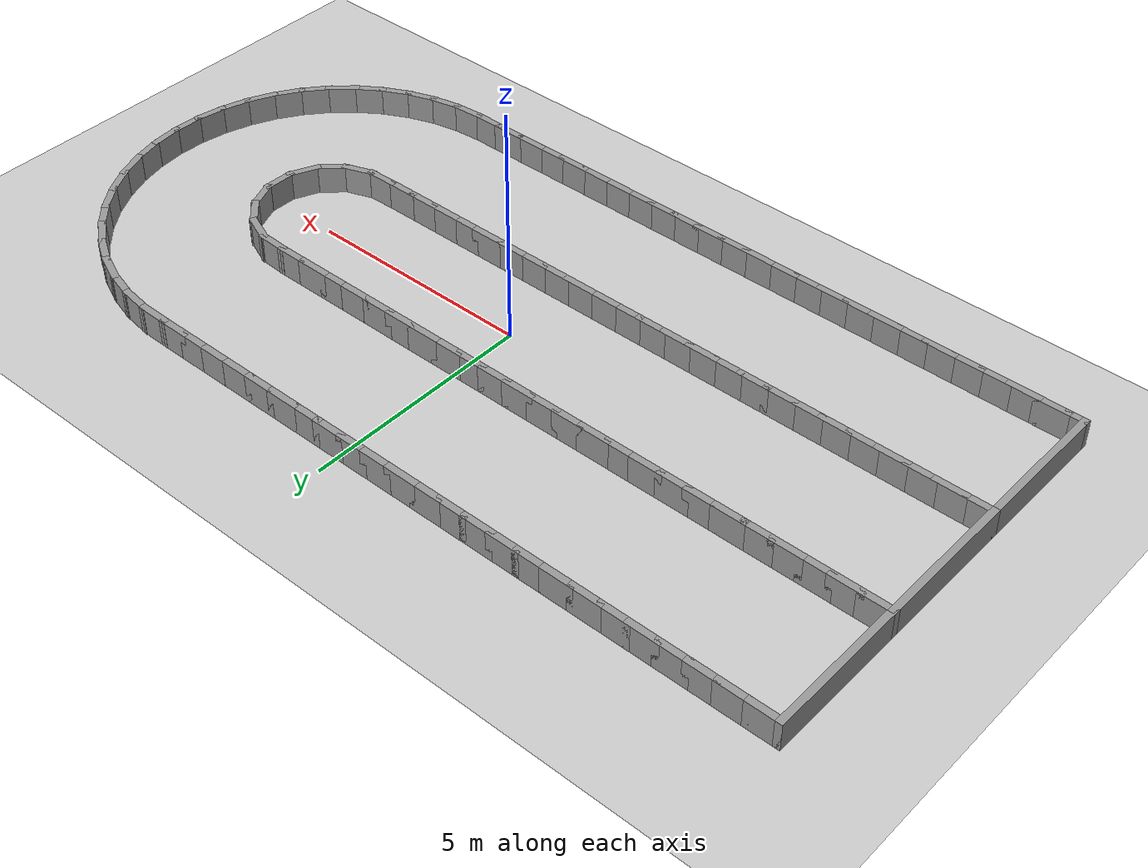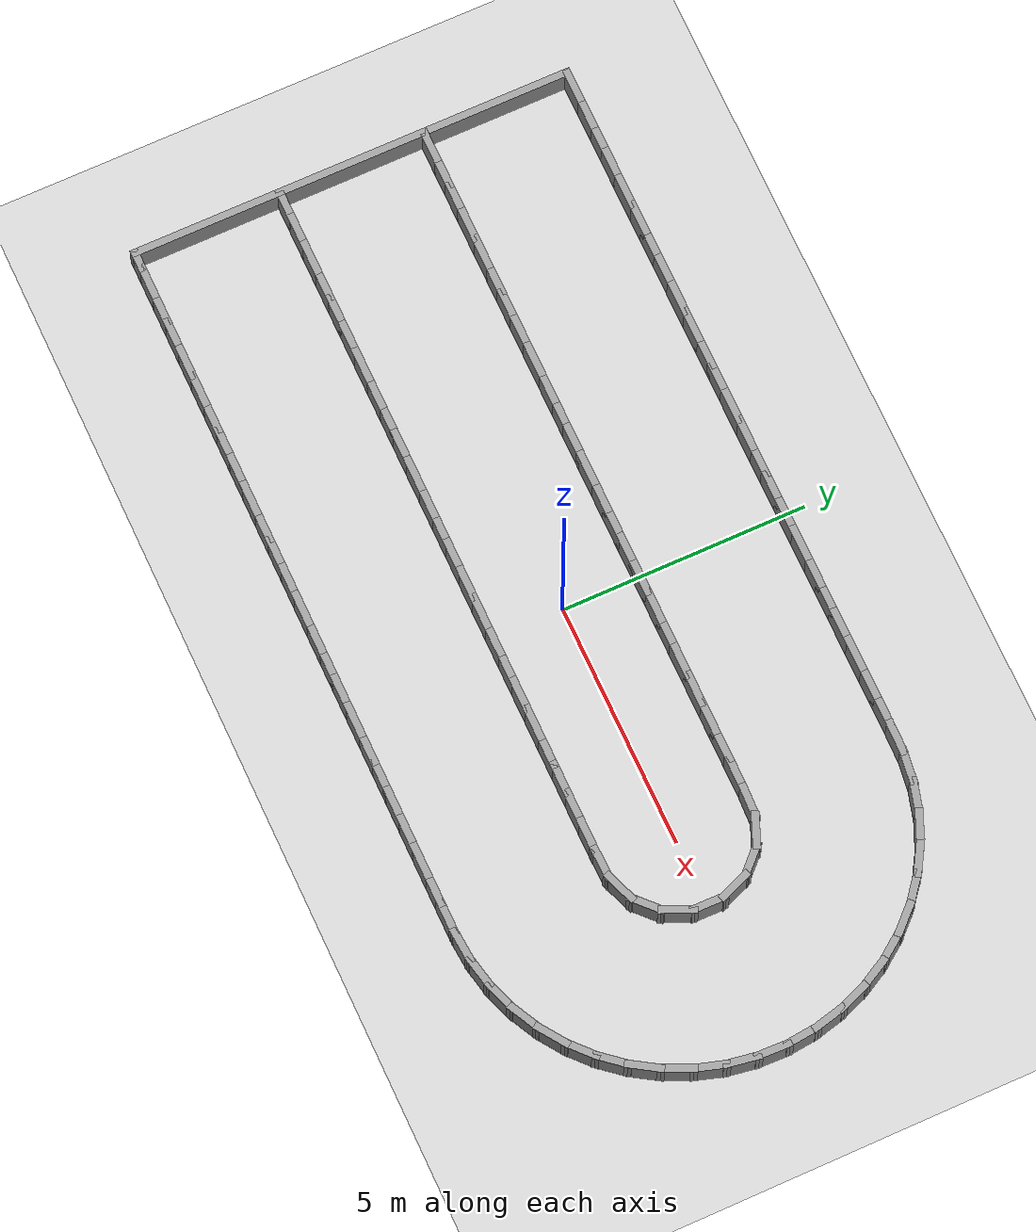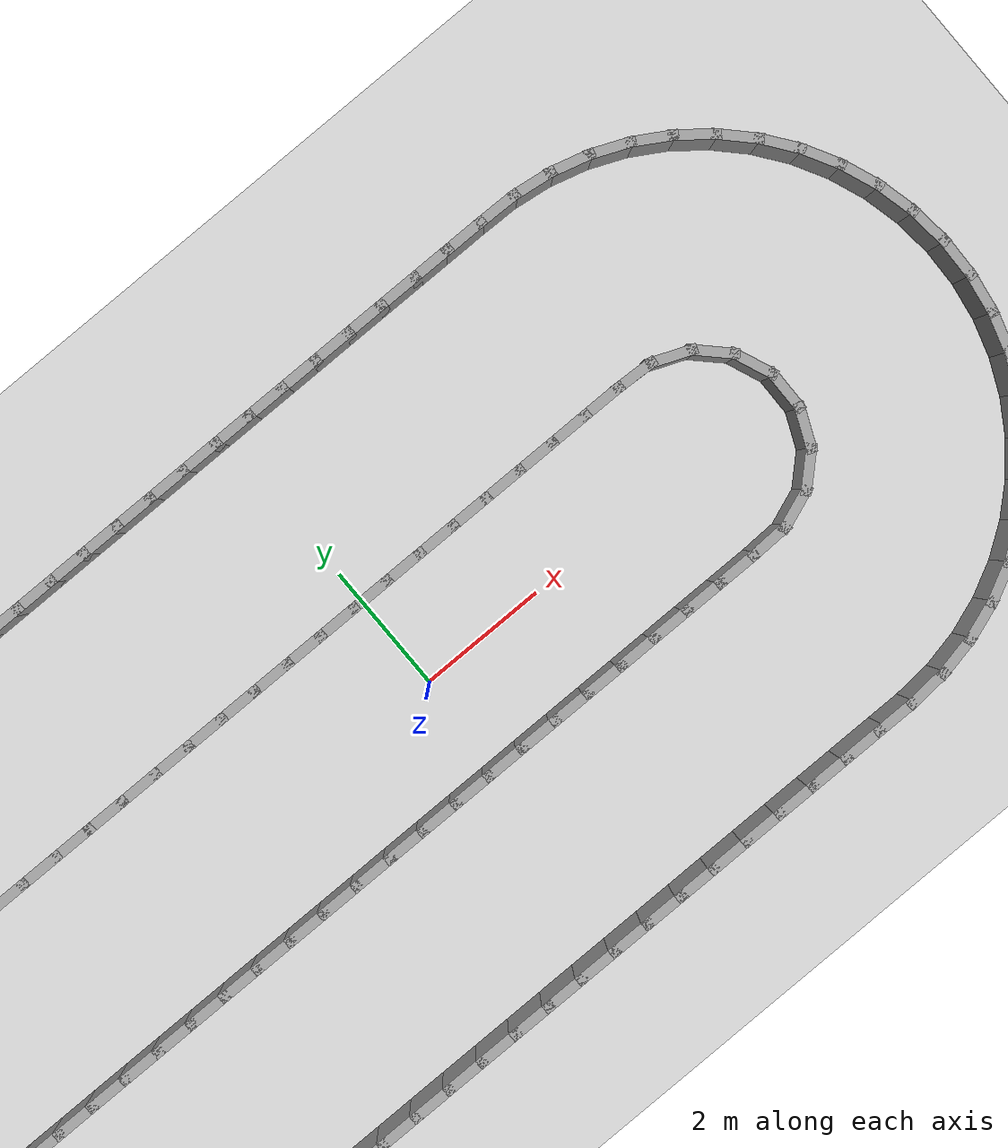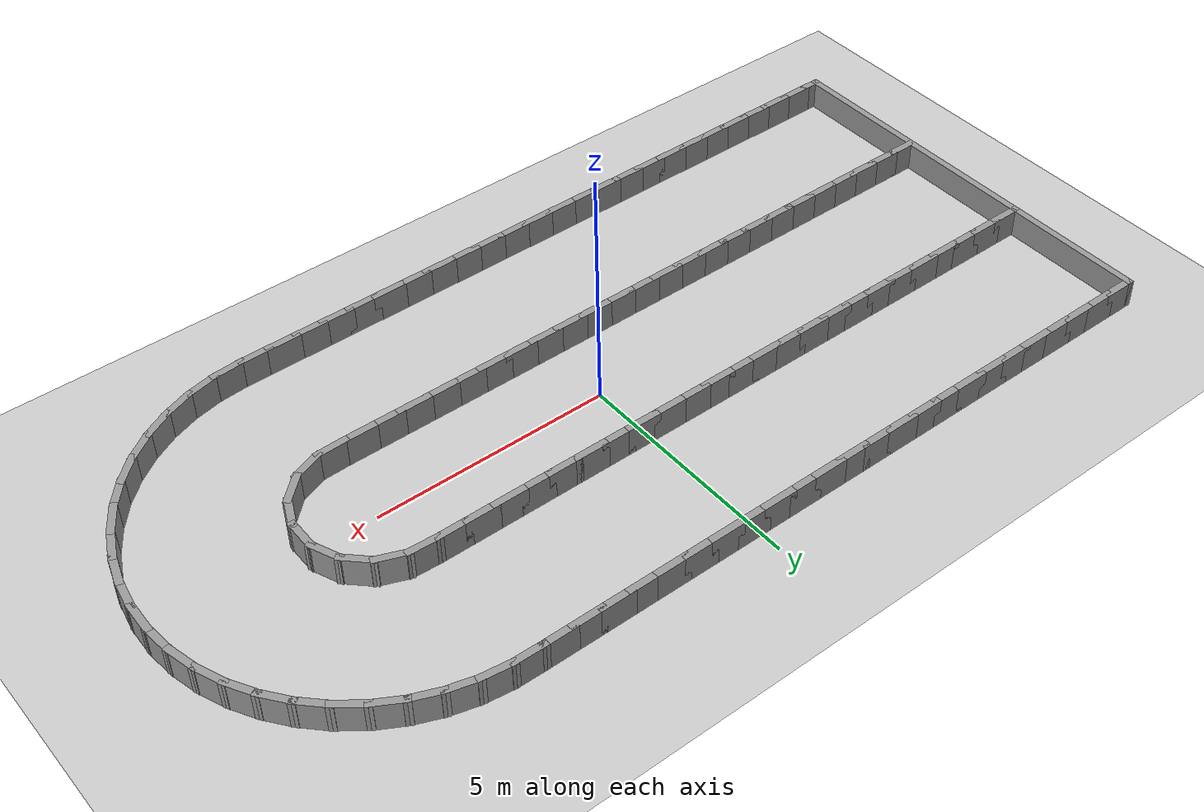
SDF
<?xml version="1.0" ?>
<sdf version='1.7'>
  <world name='default'>
    <plugin name='gazebo_ros_state' filename='libgazebo_ros_state.so'>
      <ros>
        <namespace>/</namespace>
      </ros>
      <update_rate>1000.0</update_rate>
    </plugin>

    <light name='sun' type='directional'>
      <cast_shadows>1</cast_shadows>
      <pose>0 0 10 0 -0 0</pose>
      <diffuse>0.8 0.8 0.8 1</diffuse>
      <specular>0.2 0.2 0.2 1</specular>
      <attenuation>
        <range>1000</range>
        <constant>0.9</constant>
        <linear>0.01</linear>
        <quadratic>0.001</quadratic>
      </attenuation>
      <direction>-0.5 0.1 -0.9</direction>
      <spot>
        <inner_angle>0</inner_angle>
        <outer_angle>0</outer_angle>
        <falloff>0</falloff>
      </spot>
    </light>
    <model name='ground_plane'>
      <static>1</static>
      <link name='link'>
        <collision name='collision'>
          <geometry>
            <plane>
              <normal>0 0 1</normal>
              <size>100 100</size>
            </plane>
          </geometry>
          <surface>
            <friction>
              <ode>
                <mu>100</mu>
                <mu2>50</mu2>
              </ode>
              <torsional>
                <ode/>
              </torsional>
            </friction>
            <contact>
              <ode/>
            </contact>
            <bounce/>
          </surface>
          <max_contacts>10</max_contacts>
        </collision>
        <visual name='visual'>
          <cast_shadows>0</cast_shadows>
          <geometry>
            <plane>
              <normal>0 0 1</normal>
              <size>100 100</size>
            </plane>
          </geometry>
          <material>
            <script>
              <uri>file://media/materials/scripts/gazebo.material</uri>
              <name>Gazebo/Grey</name>
            </script>
          </material>
        </visual>
        <self_collide>0</self_collide>
        <enable_wind>0</enable_wind>
        <kinematic>0</kinematic>
      </link>
    </model>
    <gravity>0 0 -9.8</gravity>
    <magnetic_field>6e-06 2.3e-05 -4.2e-05</magnetic_field>
    <atmosphere type='adiabatic'/>
    <physics type='ode'>
      <max_step_size>0.001</max_step_size>
      <real_time_factor>1</real_time_factor>
      <real_time_update_rate>1000</real_time_update_rate>
    </physics>
    <scene>
      <ambient>0.4 0.4 0.4 1</ambient>
      <background>0.7 0.7 0.7 1</background>
      <shadows>1</shadows>
    </scene>
    <audio>
      <device>default</device>
    </audio>
    <wind/>
    <spherical_coordinates>
      <surface_model>EARTH_WGS84</surface_model>
      <latitude_deg>0</latitude_deg>
      <longitude_deg>0</longitude_deg>
      <elevation>0</elevation>
      <heading_deg>0</heading_deg>
    </spherical_coordinates>
  <model name='hairpin_safe'>
    <pose>0 0 0 0 -0 0</pose>
    <link name='Wall_0'>
      <collision name='Wall_0_Collision'>
        <geometry><box><size>0.7500 0.1500 0.6000</size></box></geometry>
        <pose>0 0 0.3000 0 -0 0</pose>
      </collision>
      <visual name='Wall_0_Visual'>
        <pose>0 0 0.3000 0 -0 0</pose>
        <geometry><box><size>0.7500 0.1500 0.6000</size></box></geometry>
        <material>
          <script>
            <uri>file://media/materials/scripts/gazebo.material</uri>
            <name>Gazebo/Grey</name>
          </script>
          <ambient>1 1 1 1</ambient>
        </material>
      </visual>
      <pose>-9.4000 4.5000 0 0 -0 0.00000</pose>
    </link>
    <link name='Wall_1'>
      <collision name='Wall_1_Collision'>
        <geometry><box><size>0.7500 0.1500 0.6000</size></box></geometry>
        <pose>0 0 0.3000 0 -0 0</pose>
      </collision>
      <visual name='Wall_1_Visual'>
        <pose>0 0 0.3000 0 -0 0</pose>
        <geometry><box><size>0.7500 0.1500 0.6000</size></box></geometry>
        <material>
          <script>
            <uri>file://media/materials/scripts/gazebo.material</uri>
            <name>Gazebo/Grey</name>
          </script>
          <ambient>1 1 1 1</ambient>
        </material>
      </visual>
      <pose>-8.8000 4.5000 0 0 -0 0.00000</pose>
    </link>
    <link name='Wall_2'>
      <collision name='Wall_2_Collision'>
        <geometry><box><size>0.7500 0.1500 0.6000</size></box></geometry>
        <pose>0 0 0.3000 0 -0 0</pose>
      </collision>
      <visual name='Wall_2_Visual'>
        <pose>0 0 0.3000 0 -0 0</pose>
        <geometry><box><size>0.7500 0.1500 0.6000</size></box></geometry>
        <material>
          <script>
            <uri>file://media/materials/scripts/gazebo.material</uri>
            <name>Gazebo/Grey</name>
          </script>
          <ambient>1 1 1 1</ambient>
        </material>
      </visual>
      <pose>-8.2000 4.5000 0 0 -0 0.00000</pose>
    </link>
    <link name='Wall_3'>
      <collision name='Wall_3_Collision'>
        <geometry><box><size>0.7500 0.1500 0.6000</size></box></geometry>
        <pose>0 0 0.3000 0 -0 0</pose>
      </collision>
      <visual name='Wall_3_Visual'>
        <pose>0 0 0.3000 0 -0 0</pose>
        <geometry><box><size>0.7500 0.1500 0.6000</size></box></geometry>
        <material>
          <script>
            <uri>file://media/materials/scripts/gazebo.material</uri>
            <name>Gazebo/Grey</name>
          </script>
          <ambient>1 1 1 1</ambient>
        </material>
      </visual>
      <pose>-7.6000 4.5000 0 0 -0 0.00000</pose>
    </link>
    <link name='Wall_4'>
      <collision name='Wall_4_Collision'>
        <geometry><box><size>0.7500 0.1500 0.6000</size></box></geometry>
        <pose>0 0 0.3000 0 -0 0</pose>
      </collision>
      <visual name='Wall_4_Visual'>
        <pose>0 0 0.3000 0 -0 0</pose>
        <geometry><box><size>0.7500 0.1500 0.6000</size></box></geometry>
        <material>
          <script>
            <uri>file://media/materials/scripts/gazebo.material</uri>
            <name>Gazebo/Grey</name>
          </script>
          <ambient>1 1 1 1</ambient>
        </material>
      </visual>
      <pose>-7.0000 4.5000 0 0 -0 0.00000</pose>
    </link>
    <link name='Wall_5'>
      <collision name='Wall_5_Collision'>
        <geometry><box><size>0.7500 0.1500 0.6000</size></box></geometry>
        <pose>0 0 0.3000 0 -0 0</pose>
      </collision>
      <visual name='Wall_5_Visual'>
        <pose>0 0 0.3000 0 -0 0</pose>
        <geometry><box><size>0.7500 0.1500 0.6000</size></box></geometry>
        <material>
          <script>
            <uri>file://media/materials/scripts/gazebo.material</uri>
            <name>Gazebo/Grey</name>
          </script>
          <ambient>1 1 1 1</ambient>
        </material>
      </visual>
      <pose>-6.4000 4.5000 0 0 -0 0.00000</pose>
    </link>
    <link name='Wall_6'>
      <collision name='Wall_6_Collision'>
        <geometry><box><size>0.7500 0.1500 0.6000</size></box></geometry>
        <pose>0 0 0.3000 0 -0 0</pose>
      </collision>
      <visual name='Wall_6_Visual'>
        <pose>0 0 0.3000 0 -0 0</pose>
        <geometry><box><size>0.7500 0.1500 0.6000</size></box></geometry>
        <material>
          <script>
            <uri>file://media/materials/scripts/gazebo.material</uri>
            <name>Gazebo/Grey</name>
          </script>
          <ambient>1 1 1 1</ambient>
        </material>
      </visual>
      <pose>-5.8000 4.5000 0 0 -0 0.00000</pose>
    </link>
    <link name='Wall_7'>
      <collision name='Wall_7_Collision'>
        <geometry><box><size>0.7500 0.1500 0.6000</size></box></geometry>
        <pose>0 0 0.3000 0 -0 0</pose>
      </collision>
      <visual name='Wall_7_Visual'>
        <pose>0 0 0.3000 0 -0 0</pose>
        <geometry><box><size>0.7500 0.1500 0.6000</size></box></geometry>
        <material>
          <script>
            <uri>file://media/materials/scripts/gazebo.material</uri>
            <name>Gazebo/Grey</name>
          </script>
          <ambient>1 1 1 1</ambient>
        </material>
      </visual>
      <pose>-5.2000 4.5000 0 0 -0 0.00000</pose>
    </link>
    <link name='Wall_8'>
      <collision name='Wall_8_Collision'>
        <geometry><box><size>0.7500 0.1500 0.6000</size></box></geometry>
        <pose>0 0 0.3000 0 -0 0</pose>
      </collision>
      <visual name='Wall_8_Visual'>
        <pose>0 0 0.3000 0 -0 0</pose>
        <geometry><box><size>0.7500 0.1500 0.6000</size></box></geometry>
        <material>
          <script>
            <uri>file://media/materials/scripts/gazebo.material</uri>
            <name>Gazebo/Grey</name>
          </script>
          <ambient>1 1 1 1</ambient>
        </material>
      </visual>
      <pose>-4.6000 4.5000 0 0 -0 0.00000</pose>
    </link>
    <link name='Wall_9'>
      <collision name='Wall_9_Collision'>
        <geometry><box><size>0.7500 0.1500 0.6000</size></box></geometry>
        <pose>0 0 0.3000 0 -0 0</pose>
      </collision>
      <visual name='Wall_9_Visual'>
        <pose>0 0 0.3000 0 -0 0</pose>
        <geometry><box><size>0.7500 0.1500 0.6000</size></box></geometry>
        <material>
          <script>
            <uri>file://media/materials/scripts/gazebo.material</uri>
            <name>Gazebo/Grey</name>
          </script>
          <ambient>1 1 1 1</ambient>
        </material>
      </visual>
      <pose>-4.0000 4.5000 0 0 -0 0.00000</pose>
    </link>
    <link name='Wall_10'>
      <collision name='Wall_10_Collision'>
        <geometry><box><size>0.7500 0.1500 0.6000</size></box></geometry>
        <pose>0 0 0.3000 0 -0 0</pose>
      </collision>
      <visual name='Wall_10_Visual'>
        <pose>0 0 0.3000 0 -0 0</pose>
        <geometry><box><size>0.7500 0.1500 0.6000</size></box></geometry>
        <material>
          <script>
            <uri>file://media/materials/scripts/gazebo.material</uri>
            <name>Gazebo/Grey</name>
          </script>
          <ambient>1 1 1 1</ambient>
        </material>
      </visual>
      <pose>-3.4000 4.5000 0 0 -0 0.00000</pose>
    </link>
    <link name='Wall_11'>
      <collision name='Wall_11_Collision'>
        <geometry><box><size>0.7500 0.1500 0.6000</size></box></geometry>
        <pose>0 0 0.3000 0 -0 0</pose>
      </collision>
      <visual name='Wall_11_Visual'>
        <pose>0 0 0.3000 0 -0 0</pose>
        <geometry><box><size>0.7500 0.1500 0.6000</size></box></geometry>
        <material>
          <script>
            <uri>file://media/materials/scripts/gazebo.material</uri>
            <name>Gazebo/Grey</name>
          </script>
          <ambient>1 1 1 1</ambient>
        </material>
      </visual>
      <pose>-2.8000 4.5000 0 0 -0 0.00000</pose>
    </link>
    <link name='Wall_12'>
      <collision name='Wall_12_Collision'>
        <geometry><box><size>0.7500 0.1500 0.6000</size></box></geometry>
        <pose>0 0 0.3000 0 -0 0</pose>
      </collision>
      <visual name='Wall_12_Visual'>
        <pose>0 0 0.3000 0 -0 0</pose>
        <geometry><box><size>0.7500 0.1500 0.6000</size></box></geometry>
        <material>
          <script>
            <uri>file://media/materials/scripts/gazebo.material</uri>
            <name>Gazebo/Grey</name>
          </script>
          <ambient>1 1 1 1</ambient>
        </material>
      </visual>
      <pose>-2.2000 4.5000 0 0 -0 0.00000</pose>
    </link>
    <link name='Wall_13'>
      <collision name='Wall_13_Collision'>
        <geometry><box><size>0.7500 0.1500 0.6000</size></box></geometry>
        <pose>0 0 0.3000 0 -0 0</pose>
      </collision>
      <visual name='Wall_13_Visual'>
        <pose>0 0 0.3000 0 -0 0</pose>
        <geometry><box><size>0.7500 0.1500 0.6000</size></box></geometry>
        <material>
          <script>
            <uri>file://media/materials/scripts/gazebo.material</uri>
            <name>Gazebo/Grey</name>
          </script>
          <ambient>1 1 1 1</ambient>
        </material>
      </visual>
      <pose>-1.6000 4.5000 0 0 -0 0.00000</pose>
    </link>
    <link name='Wall_14'>
      <collision name='Wall_14_Collision'>
        <geometry><box><size>0.7500 0.1500 0.6000</size></box></geometry>
        <pose>0 0 0.3000 0 -0 0</pose>
      </collision>
      <visual name='Wall_14_Visual'>
        <pose>0 0 0.3000 0 -0 0</pose>
        <geometry><box><size>0.7500 0.1500 0.6000</size></box></geometry>
        <material>
          <script>
            <uri>file://media/materials/scripts/gazebo.material</uri>
            <name>Gazebo/Grey</name>
          </script>
          <ambient>1 1 1 1</ambient>
        </material>
      </visual>
      <pose>-1.0000 4.5000 0 0 -0 0.00000</pose>
    </link>
    <link name='Wall_15'>
      <collision name='Wall_15_Collision'>
        <geometry><box><size>0.7500 0.1500 0.6000</size></box></geometry>
        <pose>0 0 0.3000 0 -0 0</pose>
      </collision>
      <visual name='Wall_15_Visual'>
        <pose>0 0 0.3000 0 -0 0</pose>
        <geometry><box><size>0.7500 0.1500 0.6000</size></box></geometry>
        <material>
          <script>
            <uri>file://media/materials/scripts/gazebo.material</uri>
            <name>Gazebo/Grey</name>
          </script>
          <ambient>1 1 1 1</ambient>
        </material>
      </visual>
      <pose>-0.4000 4.5000 0 0 -0 0.00000</pose>
    </link>
    <link name='Wall_16'>
      <collision name='Wall_16_Collision'>
        <geometry><box><size>0.7500 0.1500 0.6000</size></box></geometry>
        <pose>0 0 0.3000 0 -0 0</pose>
      </collision>
      <visual name='Wall_16_Visual'>
        <pose>0 0 0.3000 0 -0 0</pose>
        <geometry><box><size>0.7500 0.1500 0.6000</size></box></geometry>
        <material>
          <script>
            <uri>file://media/materials/scripts/gazebo.material</uri>
            <name>Gazebo/Grey</name>
          </script>
          <ambient>1 1 1 1</ambient>
        </material>
      </visual>
      <pose>0.2000 4.5000 0 0 -0 0.00000</pose>
    </link>
    <link name='Wall_17'>
      <collision name='Wall_17_Collision'>
        <geometry><box><size>0.7500 0.1500 0.6000</size></box></geometry>
        <pose>0 0 0.3000 0 -0 0</pose>
      </collision>
      <visual name='Wall_17_Visual'>
        <pose>0 0 0.3000 0 -0 0</pose>
        <geometry><box><size>0.7500 0.1500 0.6000</size></box></geometry>
        <material>
          <script>
            <uri>file://media/materials/scripts/gazebo.material</uri>
            <name>Gazebo/Grey</name>
          </script>
          <ambient>1 1 1 1</ambient>
        </material>
      </visual>
      <pose>0.8000 4.5000 0 0 -0 0.00000</pose>
    </link>
    <link name='Wall_18'>
      <collision name='Wall_18_Collision'>
        <geometry><box><size>0.7500 0.1500 0.6000</size></box></geometry>
        <pose>0 0 0.3000 0 -0 0</pose>
      </collision>
      <visual name='Wall_18_Visual'>
        <pose>0 0 0.3000 0 -0 0</pose>
        <geometry><box><size>0.7500 0.1500 0.6000</size></box></geometry>
        <material>
          <script>
            <uri>file://media/materials/scripts/gazebo.material</uri>
            <name>Gazebo/Grey</name>
          </script>
          <ambient>1 1 1 1</ambient>
        </material>
      </visual>
      <pose>1.4000 4.5000 0 0 -0 0.00000</pose>
    </link>
    <link name='Wall_19'>
      <collision name='Wall_19_Collision'>
        <geometry><box><size>0.7500 0.1500 0.6000</size></box></geometry>
        <pose>0 0 0.3000 0 -0 0</pose>
      </collision>
      <visual name='Wall_19_Visual'>
        <pose>0 0 0.3000 0 -0 0</pose>
        <geometry><box><size>0.7500 0.1500 0.6000</size></box></geometry>
        <material>
          <script>
            <uri>file://media/materials/scripts/gazebo.material</uri>
            <name>Gazebo/Grey</name>
          </script>
          <ambient>1 1 1 1</ambient>
        </material>
      </visual>
      <pose>2.0000 4.5000 0 0 -0 0.00000</pose>
    </link>
    <link name='Wall_20'>
      <collision name='Wall_20_Collision'>
        <geometry><box><size>0.7500 0.1500 0.6000</size></box></geometry>
        <pose>0 0 0.3000 0 -0 0</pose>
      </collision>
      <visual name='Wall_20_Visual'>
        <pose>0 0 0.3000 0 -0 0</pose>
        <geometry><box><size>0.7500 0.1500 0.6000</size></box></geometry>
        <material>
          <script>
            <uri>file://media/materials/scripts/gazebo.material</uri>
            <name>Gazebo/Grey</name>
          </script>
          <ambient>1 1 1 1</ambient>
        </material>
      </visual>
      <pose>2.6000 4.5000 0 0 -0 0.00000</pose>
    </link>
    <link name='Wall_21'>
      <collision name='Wall_21_Collision'>
        <geometry><box><size>0.7500 0.1500 0.6000</size></box></geometry>
        <pose>0 0 0.3000 0 -0 0</pose>
      </collision>
      <visual name='Wall_21_Visual'>
        <pose>0 0 0.3000 0 -0 0</pose>
        <geometry><box><size>0.7500 0.1500 0.6000</size></box></geometry>
        <material>
          <script>
            <uri>file://media/materials/scripts/gazebo.material</uri>
            <name>Gazebo/Grey</name>
          </script>
          <ambient>1 1 1 1</ambient>
        </material>
      </visual>
      <pose>3.2000 4.5000 0 0 -0 0.00000</pose>
    </link>
    <link name='Wall_22'>
      <collision name='Wall_22_Collision'>
        <geometry><box><size>0.7500 0.1500 0.6000</size></box></geometry>
        <pose>0 0 0.3000 0 -0 0</pose>
      </collision>
      <visual name='Wall_22_Visual'>
        <pose>0 0 0.3000 0 -0 0</pose>
        <geometry><box><size>0.7500 0.1500 0.6000</size></box></geometry>
        <material>
          <script>
            <uri>file://media/materials/scripts/gazebo.material</uri>
            <name>Gazebo/Grey</name>
          </script>
          <ambient>1 1 1 1</ambient>
        </material>
      </visual>
      <pose>3.8000 4.5000 0 0 -0 0.00000</pose>
    </link>
    <link name='Wall_23'>
      <collision name='Wall_23_Collision'>
        <geometry><box><size>0.7500 0.1500 0.6000</size></box></geometry>
        <pose>0 0 0.3000 0 -0 0</pose>
      </collision>
      <visual name='Wall_23_Visual'>
        <pose>0 0 0.3000 0 -0 0</pose>
        <geometry><box><size>0.7500 0.1500 0.6000</size></box></geometry>
        <material>
          <script>
            <uri>file://media/materials/scripts/gazebo.material</uri>
            <name>Gazebo/Grey</name>
          </script>
          <ambient>1 1 1 1</ambient>
        </material>
      </visual>
      <pose>4.4000 4.5000 0 0 -0 0.00000</pose>
    </link>
    <link name='Wall_24'>
      <collision name='Wall_24_Collision'>
        <geometry><box><size>0.7499 0.1500 0.6000</size></box></geometry>
        <pose>0 0 0.3000 0 -0 0</pose>
      </collision>
      <visual name='Wall_24_Visual'>
        <pose>0 0 0.3000 0 -0 0</pose>
        <geometry><box><size>0.7499 0.1500 0.6000</size></box></geometry>
        <material>
          <script>
            <uri>file://media/materials/scripts/gazebo.material</uri>
            <name>Gazebo/Grey</name>
          </script>
          <ambient>1 1 1 1</ambient>
        </material>
      </visual>
      <pose>4.9999 4.4950 0 0 -0 -0.01683</pose>
    </link>
    <link name='Wall_25'>
      <collision name='Wall_25_Collision'>
        <geometry><box><size>0.7495 0.1500 0.6000</size></box></geometry>
        <pose>0 0 0.3000 0 -0 0</pose>
      </collision>
      <visual name='Wall_25_Visual'>
        <pose>0 0 0.3000 0 -0 0</pose>
        <geometry><box><size>0.7495 0.1500 0.6000</size></box></geometry>
        <material>
          <script>
            <uri>file://media/materials/scripts/gazebo.material</uri>
            <name>Gazebo/Grey</name>
          </script>
          <ambient>1 1 1 1</ambient>
        </material>
      </visual>
      <pose>5.5969 4.4500 0 0 -0 -0.13338</pose>
    </link>
    <link name='Wall_26'>
      <collision name='Wall_26_Collision'>
        <geometry><box><size>0.7495 0.1500 0.6000</size></box></geometry>
        <pose>0 0 0.3000 0 -0 0</pose>
      </collision>
      <visual name='Wall_26_Visual'>
        <pose>0 0 0.3000 0 -0 0</pose>
        <geometry><box><size>0.7495 0.1500 0.6000</size></box></geometry>
        <material>
          <script>
            <uri>file://media/materials/scripts/gazebo.material</uri>
            <name>Gazebo/Grey</name>
          </script>
          <ambient>1 1 1 1</ambient>
        </material>
      </visual>
      <pose>6.1832 4.3312 0 0 -0 -0.26656</pose>
    </link>
    <link name='Wall_27'>
      <collision name='Wall_27_Collision'>
        <geometry><box><size>0.7495 0.1500 0.6000</size></box></geometry>
        <pose>0 0 0.3000 0 -0 0</pose>
      </collision>
      <visual name='Wall_27_Visual'>
        <pose>0 0 0.3000 0 -0 0</pose>
        <geometry><box><size>0.7495 0.1500 0.6000</size></box></geometry>
        <material>
          <script>
            <uri>file://media/materials/scripts/gazebo.material</uri>
            <name>Gazebo/Grey</name>
          </script>
          <ambient>1 1 1 1</ambient>
        </material>
      </visual>
      <pose>6.7485 4.1355 0 0 -0 -0.40014</pose>
    </link>
    <link name='Wall_28'>
      <collision name='Wall_28_Collision'>
        <geometry><box><size>0.7496 0.1500 0.6000</size></box></geometry>
        <pose>0 0 0.3000 0 -0 0</pose>
      </collision>
      <visual name='Wall_28_Visual'>
        <pose>0 0 0.3000 0 -0 0</pose>
        <geometry><box><size>0.7496 0.1500 0.6000</size></box></geometry>
        <material>
          <script>
            <uri>file://media/materials/scripts/gazebo.material</uri>
            <name>Gazebo/Grey</name>
          </script>
          <ambient>1 1 1 1</ambient>
        </material>
      </visual>
      <pose>7.2827 3.8663 0 0 -0 -0.53312</pose>
    </link>
    <link name='Wall_29'>
      <collision name='Wall_29_Collision'>
        <geometry><box><size>0.7496 0.1500 0.6000</size></box></geometry>
        <pose>0 0 0.3000 0 -0 0</pose>
      </collision>
      <visual name='Wall_29_Visual'>
        <pose>0 0 0.3000 0 -0 0</pose>
        <geometry><box><size>0.7496 0.1500 0.6000</size></box></geometry>
        <material>
          <script>
            <uri>file://media/materials/scripts/gazebo.material</uri>
            <name>Gazebo/Grey</name>
          </script>
          <ambient>1 1 1 1</ambient>
        </material>
      </visual>
      <pose>7.7765 3.5286 0 0 -0 -0.66690</pose>
    </link>
    <link name='Wall_30'>
      <collision name='Wall_30_Collision'>
        <geometry><box><size>0.7495 0.1500 0.6000</size></box></geometry>
        <pose>0 0 0.3000 0 -0 0</pose>
      </collision>
      <visual name='Wall_30_Visual'>
        <pose>0 0 0.3000 0 -0 0</pose>
        <geometry><box><size>0.7495 0.1500 0.6000</size></box></geometry>
        <material>
          <script>
            <uri>file://media/materials/scripts/gazebo.material</uri>
            <name>Gazebo/Grey</name>
          </script>
          <ambient>1 1 1 1</ambient>
        </material>
      </visual>
      <pose>8.2209 3.1281 0 0 -0 -0.79986</pose>
    </link>
    <link name='Wall_31'>
      <collision name='Wall_31_Collision'>
        <geometry><box><size>0.7495 0.1500 0.6000</size></box></geometry>
        <pose>0 0 0.3000 0 -0 0</pose>
      </collision>
      <visual name='Wall_31_Visual'>
        <pose>0 0 0.3000 0 -0 0</pose>
        <geometry><box><size>0.7495 0.1500 0.6000</size></box></geometry>
        <material>
          <script>
            <uri>file://media/materials/scripts/gazebo.material</uri>
            <name>Gazebo/Grey</name>
          </script>
          <ambient>1 1 1 1</ambient>
        </material>
      </visual>
      <pose>8.6082 2.6722 0 0 -0 -0.93347</pose>
    </link>
    <link name='Wall_32'>
      <collision name='Wall_32_Collision'>
        <geometry><box><size>0.7495 0.1500 0.6000</size></box></geometry>
        <pose>0 0 0.3000 0 -0 0</pose>
      </collision>
      <visual name='Wall_32_Visual'>
        <pose>0 0 0.3000 0 -0 0</pose>
        <geometry><box><size>0.7495 0.1500 0.6000</size></box></geometry>
        <material>
          <script>
            <uri>file://media/materials/scripts/gazebo.material</uri>
            <name>Gazebo/Grey</name>
          </script>
          <ambient>1 1 1 1</ambient>
        </material>
      </visual>
      <pose>8.9314 2.1688 0 0 -0 -1.06662</pose>
    </link>
    <link name='Wall_33'>
      <collision name='Wall_33_Collision'>
        <geometry><box><size>0.7495 0.1500 0.6000</size></box></geometry>
        <pose>0 0 0.3000 0 -0 0</pose>
      </collision>
      <visual name='Wall_33_Visual'>
        <pose>0 0 0.3000 0 -0 0</pose>
        <geometry><box><size>0.7495 0.1500 0.6000</size></box></geometry>
        <material>
          <script>
            <uri>file://media/materials/scripts/gazebo.material</uri>
            <name>Gazebo/Grey</name>
          </script>
          <ambient>1 1 1 1</ambient>
        </material>
      </visual>
      <pose>9.1848 1.6269 0 0 -0 -1.20003</pose>
    </link>
    <link name='Wall_34'>
      <collision name='Wall_34_Collision'>
        <geometry><box><size>0.7495 0.1500 0.6000</size></box></geometry>
        <pose>0 0 0.3000 0 -0 0</pose>
      </collision>
      <visual name='Wall_34_Visual'>
        <pose>0 0 0.3000 0 -0 0</pose>
        <geometry><box><size>0.7495 0.1500 0.6000</size></box></geometry>
        <material>
          <script>
            <uri>file://media/materials/scripts/gazebo.material</uri>
            <name>Gazebo/Grey</name>
          </script>
          <ambient>1 1 1 1</ambient>
        </material>
      </visual>
      <pose>9.3639 1.0561 0 0 -0 -1.33338</pose>
    </link>
    <link name='Wall_35'>
      <collision name='Wall_35_Collision'>
        <geometry><box><size>0.7495 0.1500 0.6000</size></box></geometry>
        <pose>0 0 0.3000 0 -0 0</pose>
      </collision>
      <visual name='Wall_35_Visual'>
        <pose>0 0 0.3000 0 -0 0</pose>
        <geometry><box><size>0.7495 0.1500 0.6000</size></box></geometry>
        <material>
          <script>
            <uri>file://media/materials/scripts/gazebo.material</uri>
            <name>Gazebo/Grey</name>
          </script>
          <ambient>1 1 1 1</ambient>
        </material>
      </visual>
      <pose>9.4656 0.4666 0 0 -0 -1.46658</pose>
    </link>
    <link name='Wall_36'>
      <collision name='Wall_36_Collision'>
        <geometry><box><size>0.7495 0.1500 0.6000</size></box></geometry>
        <pose>0 0 0.3000 0 -0 0</pose>
      </collision>
      <visual name='Wall_36_Visual'>
        <pose>0 0 0.3000 0 -0 0</pose>
        <geometry><box><size>0.7495 0.1500 0.6000</size></box></geometry>
        <material>
          <script>
            <uri>file://media/materials/scripts/gazebo.material</uri>
            <name>Gazebo/Grey</name>
          </script>
          <ambient>1 1 1 1</ambient>
        </material>
      </visual>
      <pose>9.4880 -0.1312 0 0 -0 -1.60014</pose>
    </link>
    <link name='Wall_37'>
      <collision name='Wall_37_Collision'>
        <geometry><box><size>0.7496 0.1500 0.6000</size></box></geometry>
        <pose>0 0 0.3000 0 -0 0</pose>
      </collision>
      <visual name='Wall_37_Visual'>
        <pose>0 0 0.3000 0 -0 0</pose>
        <geometry><box><size>0.7496 0.1500 0.6000</size></box></geometry>
        <material>
          <script>
            <uri>file://media/materials/scripts/gazebo.material</uri>
            <name>Gazebo/Grey</name>
          </script>
          <ambient>1 1 1 1</ambient>
        </material>
      </visual>
      <pose>9.4307 -0.7267 0 0 -0 -1.73314</pose>
    </link>
    <link name='Wall_38'>
      <collision name='Wall_38_Collision'>
        <geometry><box><size>0.7496 0.1500 0.6000</size></box></geometry>
        <pose>0 0 0.3000 0 -0 0</pose>
      </collision>
      <visual name='Wall_38_Visual'>
        <pose>0 0 0.3000 0 -0 0</pose>
        <geometry><box><size>0.7496 0.1500 0.6000</size></box></geometry>
        <material>
          <script>
            <uri>file://media/materials/scripts/gazebo.material</uri>
            <name>Gazebo/Grey</name>
          </script>
          <ambient>1 1 1 1</ambient>
        </material>
      </visual>
      <pose>9.2948 -1.3092 0 0 -0 -1.86690</pose>
    </link>
    <link name='Wall_39'>
      <collision name='Wall_39_Collision'>
        <geometry><box><size>0.7495 0.1500 0.6000</size></box></geometry>
        <pose>0 0 0.3000 0 -0 0</pose>
      </collision>
      <visual name='Wall_39_Visual'>
        <pose>0 0 0.3000 0 -0 0</pose>
        <geometry><box><size>0.7495 0.1500 0.6000</size></box></geometry>
        <material>
          <script>
            <uri>file://media/materials/scripts/gazebo.material</uri>
            <name>Gazebo/Grey</name>
          </script>
          <ambient>1 1 1 1</ambient>
        </material>
      </visual>
      <pose>9.0826 -1.8686 0 0 -0 -1.99986</pose>
    </link>
    <link name='Wall_40'>
      <collision name='Wall_40_Collision'>
        <geometry><box><size>0.7495 0.1500 0.6000</size></box></geometry>
        <pose>0 0 0.3000 0 -0 0</pose>
      </collision>
      <visual name='Wall_40_Visual'>
        <pose>0 0 0.3000 0 -0 0</pose>
        <geometry><box><size>0.7495 0.1500 0.6000</size></box></geometry>
        <material>
          <script>
            <uri>file://media/materials/scripts/gazebo.material</uri>
            <name>Gazebo/Grey</name>
          </script>
          <ambient>1 1 1 1</ambient>
        </material>
      </visual>
      <pose>8.7980 -2.3947 0 0 -0 -2.13349</pose>
    </link>
    <link name='Wall_41'>
      <collision name='Wall_41_Collision'>
        <geometry><box><size>0.7495 0.1500 0.6000</size></box></geometry>
        <pose>0 0 0.3000 0 -0 0</pose>
      </collision>
      <visual name='Wall_41_Visual'>
        <pose>0 0 0.3000 0 -0 0</pose>
        <geometry><box><size>0.7495 0.1500 0.6000</size></box></geometry>
        <material>
          <script>
            <uri>file://media/materials/scripts/gazebo.material</uri>
            <name>Gazebo/Grey</name>
          </script>
          <ambient>1 1 1 1</ambient>
        </material>
      </visual>
      <pose>8.4459 -2.8783 0 0 -0 -2.26662</pose>
    </link>
    <link name='Wall_42'>
      <collision name='Wall_42_Collision'>
        <geometry><box><size>0.7495 0.1500 0.6000</size></box></geometry>
        <pose>0 0 0.3000 0 -0 0</pose>
      </collision>
      <visual name='Wall_42_Visual'>
        <pose>0 0 0.3000 0 -0 0</pose>
        <geometry><box><size>0.7495 0.1500 0.6000</size></box></geometry>
        <material>
          <script>
            <uri>file://media/materials/scripts/gazebo.material</uri>
            <name>Gazebo/Grey</name>
          </script>
          <ambient>1 1 1 1</ambient>
        </material>
      </visual>
      <pose>8.0327 -3.3109 0 0 -0 -2.40005</pose>
    </link>
    <link name='Wall_43'>
      <collision name='Wall_43_Collision'>
        <geometry><box><size>0.7495 0.1500 0.6000</size></box></geometry>
        <pose>0 0 0.3000 0 -0 0</pose>
      </collision>
      <visual name='Wall_43_Visual'>
        <pose>0 0 0.3000 0 -0 0</pose>
        <geometry><box><size>0.7495 0.1500 0.6000</size></box></geometry>
        <material>
          <script>
            <uri>file://media/materials/scripts/gazebo.material</uri>
            <name>Gazebo/Grey</name>
          </script>
          <ambient>1 1 1 1</ambient>
        </material>
      </visual>
      <pose>7.5656 -3.6847 0 0 -0 -2.53338</pose>
    </link>
    <link name='Wall_44'>
      <collision name='Wall_44_Collision'>
        <geometry><box><size>0.7495 0.1500 0.6000</size></box></geometry>
        <pose>0 0 0.3000 0 -0 0</pose>
      </collision>
      <visual name='Wall_44_Visual'>
        <pose>0 0 0.3000 0 -0 0</pose>
        <geometry><box><size>0.7495 0.1500 0.6000</size></box></geometry>
        <material>
          <script>
            <uri>file://media/materials/scripts/gazebo.material</uri>
            <name>Gazebo/Grey</name>
          </script>
          <ambient>1 1 1 1</ambient>
        </material>
      </visual>
      <pose>7.0530 -3.9931 0 0 -0 -2.66661</pose>
    </link>
    <link name='Wall_45'>
      <collision name='Wall_45_Collision'>
        <geometry><box><size>0.7495 0.1500 0.6000</size></box></geometry>
        <pose>0 0 0.3000 0 -0 0</pose>
      </collision>
      <visual name='Wall_45_Visual'>
        <pose>0 0 0.3000 0 -0 0</pose>
        <geometry><box><size>0.7495 0.1500 0.6000</size></box></geometry>
        <material>
          <script>
            <uri>file://media/materials/scripts/gazebo.material</uri>
            <name>Gazebo/Grey</name>
          </script>
          <ambient>1 1 1 1</ambient>
        </material>
      </visual>
      <pose>6.5039 -4.2305 0 0 -0 -2.80014</pose>
    </link>
    <link name='Wall_46'>
      <collision name='Wall_46_Collision'>
        <geometry><box><size>0.7496 0.1500 0.6000</size></box></geometry>
        <pose>0 0 0.3000 0 -0 0</pose>
      </collision>
      <visual name='Wall_46_Visual'>
        <pose>0 0 0.3000 0 -0 0</pose>
        <geometry><box><size>0.7496 0.1500 0.6000</size></box></geometry>
        <material>
          <script>
            <uri>file://media/materials/scripts/gazebo.material</uri>
            <name>Gazebo/Grey</name>
          </script>
          <ambient>1 1 1 1</ambient>
        </material>
      </visual>
      <pose>5.9282 -4.3929 0 0 -0 -2.93317</pose>
    </link>
    <link name='Wall_47'>
      <collision name='Wall_47_Collision'>
        <geometry><box><size>0.7496 0.1500 0.6000</size></box></geometry>
        <pose>0 0 0.3000 0 -0 0</pose>
      </collision>
      <visual name='Wall_47_Visual'>
        <pose>0 0 0.3000 0 -0 0</pose>
        <geometry><box><size>0.7496 0.1500 0.6000</size></box></geometry>
        <material>
          <script>
            <uri>file://media/materials/scripts/gazebo.material</uri>
            <name>Gazebo/Grey</name>
          </script>
          <ambient>1 1 1 1</ambient>
        </material>
      </visual>
      <pose>5.3360 -4.4774 0 0 -0 -3.06686</pose>
    </link>
    <link name='Wall_48'>
      <collision name='Wall_48_Collision'>
        <geometry><box><size>0.7500 0.1500 0.6000</size></box></geometry>
        <pose>0 0 0.3000 0 -0 0</pose>
      </collision>
      <visual name='Wall_48_Visual'>
        <pose>0 0 0.3000 0 -0 0</pose>
        <geometry><box><size>0.7500 0.1500 0.6000</size></box></geometry>
        <material>
          <script>
            <uri>file://media/materials/scripts/gazebo.material</uri>
            <name>Gazebo/Grey</name>
          </script>
          <ambient>1 1 1 1</ambient>
        </material>
      </visual>
      <pose>4.7370 -4.4999 0 0 -0 -3.14115</pose>
    </link>
    <link name='Wall_49'>
      <collision name='Wall_49_Collision'>
        <geometry><box><size>0.7500 0.1500 0.6000</size></box></geometry>
        <pose>0 0 0.3000 0 -0 0</pose>
      </collision>
      <visual name='Wall_49_Visual'>
        <pose>0 0 0.3000 0 -0 0</pose>
        <geometry><box><size>0.7500 0.1500 0.6000</size></box></geometry>
        <material>
          <script>
            <uri>file://media/materials/scripts/gazebo.material</uri>
            <name>Gazebo/Grey</name>
          </script>
          <ambient>1 1 1 1</ambient>
        </material>
      </visual>
      <pose>4.1370 -4.5000 0 0 -0 3.14159</pose>
    </link>
    <link name='Wall_50'>
      <collision name='Wall_50_Collision'>
        <geometry><box><size>0.7500 0.1500 0.6000</size></box></geometry>
        <pose>0 0 0.3000 0 -0 0</pose>
      </collision>
      <visual name='Wall_50_Visual'>
        <pose>0 0 0.3000 0 -0 0</pose>
        <geometry><box><size>0.7500 0.1500 0.6000</size></box></geometry>
        <material>
          <script>
            <uri>file://media/materials/scripts/gazebo.material</uri>
            <name>Gazebo/Grey</name>
          </script>
          <ambient>1 1 1 1</ambient>
        </material>
      </visual>
      <pose>3.5370 -4.5000 0 0 -0 3.14159</pose>
    </link>
    <link name='Wall_51'>
      <collision name='Wall_51_Collision'>
        <geometry><box><size>0.7500 0.1500 0.6000</size></box></geometry>
        <pose>0 0 0.3000 0 -0 0</pose>
      </collision>
      <visual name='Wall_51_Visual'>
        <pose>0 0 0.3000 0 -0 0</pose>
        <geometry><box><size>0.7500 0.1500 0.6000</size></box></geometry>
        <material>
          <script>
            <uri>file://media/materials/scripts/gazebo.material</uri>
            <name>Gazebo/Grey</name>
          </script>
          <ambient>1 1 1 1</ambient>
        </material>
      </visual>
      <pose>2.9370 -4.5000 0 0 -0 3.14159</pose>
    </link>
    <link name='Wall_52'>
      <collision name='Wall_52_Collision'>
        <geometry><box><size>0.7500 0.1500 0.6000</size></box></geometry>
        <pose>0 0 0.3000 0 -0 0</pose>
      </collision>
      <visual name='Wall_52_Visual'>
        <pose>0 0 0.3000 0 -0 0</pose>
        <geometry><box><size>0.7500 0.1500 0.6000</size></box></geometry>
        <material>
          <script>
            <uri>file://media/materials/scripts/gazebo.material</uri>
            <name>Gazebo/Grey</name>
          </script>
          <ambient>1 1 1 1</ambient>
        </material>
      </visual>
      <pose>2.3370 -4.5000 0 0 -0 3.14159</pose>
    </link>
    <link name='Wall_53'>
      <collision name='Wall_53_Collision'>
        <geometry><box><size>0.7500 0.1500 0.6000</size></box></geometry>
        <pose>0 0 0.3000 0 -0 0</pose>
      </collision>
      <visual name='Wall_53_Visual'>
        <pose>0 0 0.3000 0 -0 0</pose>
        <geometry><box><size>0.7500 0.1500 0.6000</size></box></geometry>
        <material>
          <script>
            <uri>file://media/materials/scripts/gazebo.material</uri>
            <name>Gazebo/Grey</name>
          </script>
          <ambient>1 1 1 1</ambient>
        </material>
      </visual>
      <pose>1.7370 -4.5000 0 0 -0 3.14159</pose>
    </link>
    <link name='Wall_54'>
      <collision name='Wall_54_Collision'>
        <geometry><box><size>0.7500 0.1500 0.6000</size></box></geometry>
        <pose>0 0 0.3000 0 -0 0</pose>
      </collision>
      <visual name='Wall_54_Visual'>
        <pose>0 0 0.3000 0 -0 0</pose>
        <geometry><box><size>0.7500 0.1500 0.6000</size></box></geometry>
        <material>
          <script>
            <uri>file://media/materials/scripts/gazebo.material</uri>
            <name>Gazebo/Grey</name>
          </script>
          <ambient>1 1 1 1</ambient>
        </material>
      </visual>
      <pose>1.1370 -4.5000 0 0 -0 3.14159</pose>
    </link>
    <link name='Wall_55'>
      <collision name='Wall_55_Collision'>
        <geometry><box><size>0.7500 0.1500 0.6000</size></box></geometry>
        <pose>0 0 0.3000 0 -0 0</pose>
      </collision>
      <visual name='Wall_55_Visual'>
        <pose>0 0 0.3000 0 -0 0</pose>
        <geometry><box><size>0.7500 0.1500 0.6000</size></box></geometry>
        <material>
          <script>
            <uri>file://media/materials/scripts/gazebo.material</uri>
            <name>Gazebo/Grey</name>
          </script>
          <ambient>1 1 1 1</ambient>
        </material>
      </visual>
      <pose>0.5370 -4.5000 0 0 -0 3.14159</pose>
    </link>
    <link name='Wall_56'>
      <collision name='Wall_56_Collision'>
        <geometry><box><size>0.7500 0.1500 0.6000</size></box></geometry>
        <pose>0 0 0.3000 0 -0 0</pose>
      </collision>
      <visual name='Wall_56_Visual'>
        <pose>0 0 0.3000 0 -0 0</pose>
        <geometry><box><size>0.7500 0.1500 0.6000</size></box></geometry>
        <material>
          <script>
            <uri>file://media/materials/scripts/gazebo.material</uri>
            <name>Gazebo/Grey</name>
          </script>
          <ambient>1 1 1 1</ambient>
        </material>
      </visual>
      <pose>-0.0630 -4.5000 0 0 -0 3.14159</pose>
    </link>
    <link name='Wall_57'>
      <collision name='Wall_57_Collision'>
        <geometry><box><size>0.7500 0.1500 0.6000</size></box></geometry>
        <pose>0 0 0.3000 0 -0 0</pose>
      </collision>
      <visual name='Wall_57_Visual'>
        <pose>0 0 0.3000 0 -0 0</pose>
        <geometry><box><size>0.7500 0.1500 0.6000</size></box></geometry>
        <material>
          <script>
            <uri>file://media/materials/scripts/gazebo.material</uri>
            <name>Gazebo/Grey</name>
          </script>
          <ambient>1 1 1 1</ambient>
        </material>
      </visual>
      <pose>-0.6630 -4.5000 0 0 -0 3.14159</pose>
    </link>
    <link name='Wall_58'>
      <collision name='Wall_58_Collision'>
        <geometry><box><size>0.7500 0.1500 0.6000</size></box></geometry>
        <pose>0 0 0.3000 0 -0 0</pose>
      </collision>
      <visual name='Wall_58_Visual'>
        <pose>0 0 0.3000 0 -0 0</pose>
        <geometry><box><size>0.7500 0.1500 0.6000</size></box></geometry>
        <material>
          <script>
            <uri>file://media/materials/scripts/gazebo.material</uri>
            <name>Gazebo/Grey</name>
          </script>
          <ambient>1 1 1 1</ambient>
        </material>
      </visual>
      <pose>-1.2630 -4.5000 0 0 -0 3.14159</pose>
    </link>
    <link name='Wall_59'>
      <collision name='Wall_59_Collision'>
        <geometry><box><size>0.7500 0.1500 0.6000</size></box></geometry>
        <pose>0 0 0.3000 0 -0 0</pose>
      </collision>
      <visual name='Wall_59_Visual'>
        <pose>0 0 0.3000 0 -0 0</pose>
        <geometry><box><size>0.7500 0.1500 0.6000</size></box></geometry>
        <material>
          <script>
            <uri>file://media/materials/scripts/gazebo.material</uri>
            <name>Gazebo/Grey</name>
          </script>
          <ambient>1 1 1 1</ambient>
        </material>
      </visual>
      <pose>-1.8630 -4.5000 0 0 -0 3.14159</pose>
    </link>
    <link name='Wall_60'>
      <collision name='Wall_60_Collision'>
        <geometry><box><size>0.7500 0.1500 0.6000</size></box></geometry>
        <pose>0 0 0.3000 0 -0 0</pose>
      </collision>
      <visual name='Wall_60_Visual'>
        <pose>0 0 0.3000 0 -0 0</pose>
        <geometry><box><size>0.7500 0.1500 0.6000</size></box></geometry>
        <material>
          <script>
            <uri>file://media/materials/scripts/gazebo.material</uri>
            <name>Gazebo/Grey</name>
          </script>
          <ambient>1 1 1 1</ambient>
        </material>
      </visual>
      <pose>-2.4630 -4.5000 0 0 -0 3.14159</pose>
    </link>
    <link name='Wall_61'>
      <collision name='Wall_61_Collision'>
        <geometry><box><size>0.7500 0.1500 0.6000</size></box></geometry>
        <pose>0 0 0.3000 0 -0 0</pose>
      </collision>
      <visual name='Wall_61_Visual'>
        <pose>0 0 0.3000 0 -0 0</pose>
        <geometry><box><size>0.7500 0.1500 0.6000</size></box></geometry>
        <material>
          <script>
            <uri>file://media/materials/scripts/gazebo.material</uri>
            <name>Gazebo/Grey</name>
          </script>
          <ambient>1 1 1 1</ambient>
        </material>
      </visual>
      <pose>-3.0630 -4.5000 0 0 -0 3.14159</pose>
    </link>
    <link name='Wall_62'>
      <collision name='Wall_62_Collision'>
        <geometry><box><size>0.7500 0.1500 0.6000</size></box></geometry>
        <pose>0 0 0.3000 0 -0 0</pose>
      </collision>
      <visual name='Wall_62_Visual'>
        <pose>0 0 0.3000 0 -0 0</pose>
        <geometry><box><size>0.7500 0.1500 0.6000</size></box></geometry>
        <material>
          <script>
            <uri>file://media/materials/scripts/gazebo.material</uri>
            <name>Gazebo/Grey</name>
          </script>
          <ambient>1 1 1 1</ambient>
        </material>
      </visual>
      <pose>-3.6630 -4.5000 0 0 -0 3.14159</pose>
    </link>
    <link name='Wall_63'>
      <collision name='Wall_63_Collision'>
        <geometry><box><size>0.7500 0.1500 0.6000</size></box></geometry>
        <pose>0 0 0.3000 0 -0 0</pose>
      </collision>
      <visual name='Wall_63_Visual'>
        <pose>0 0 0.3000 0 -0 0</pose>
        <geometry><box><size>0.7500 0.1500 0.6000</size></box></geometry>
        <material>
          <script>
            <uri>file://media/materials/scripts/gazebo.material</uri>
            <name>Gazebo/Grey</name>
          </script>
          <ambient>1 1 1 1</ambient>
        </material>
      </visual>
      <pose>-4.2630 -4.5000 0 0 -0 3.14159</pose>
    </link>
    <link name='Wall_64'>
      <collision name='Wall_64_Collision'>
        <geometry><box><size>0.7500 0.1500 0.6000</size></box></geometry>
        <pose>0 0 0.3000 0 -0 0</pose>
      </collision>
      <visual name='Wall_64_Visual'>
        <pose>0 0 0.3000 0 -0 0</pose>
        <geometry><box><size>0.7500 0.1500 0.6000</size></box></geometry>
        <material>
          <script>
            <uri>file://media/materials/scripts/gazebo.material</uri>
            <name>Gazebo/Grey</name>
          </script>
          <ambient>1 1 1 1</ambient>
        </material>
      </visual>
      <pose>-4.8630 -4.5000 0 0 -0 3.14159</pose>
    </link>
    <link name='Wall_65'>
      <collision name='Wall_65_Collision'>
        <geometry><box><size>0.7500 0.1500 0.6000</size></box></geometry>
        <pose>0 0 0.3000 0 -0 0</pose>
      </collision>
      <visual name='Wall_65_Visual'>
        <pose>0 0 0.3000 0 -0 0</pose>
        <geometry><box><size>0.7500 0.1500 0.6000</size></box></geometry>
        <material>
          <script>
            <uri>file://media/materials/scripts/gazebo.material</uri>
            <name>Gazebo/Grey</name>
          </script>
          <ambient>1 1 1 1</ambient>
        </material>
      </visual>
      <pose>-5.4630 -4.5000 0 0 -0 3.14159</pose>
    </link>
    <link name='Wall_66'>
      <collision name='Wall_66_Collision'>
        <geometry><box><size>0.7500 0.1500 0.6000</size></box></geometry>
        <pose>0 0 0.3000 0 -0 0</pose>
      </collision>
      <visual name='Wall_66_Visual'>
        <pose>0 0 0.3000 0 -0 0</pose>
        <geometry><box><size>0.7500 0.1500 0.6000</size></box></geometry>
        <material>
          <script>
            <uri>file://media/materials/scripts/gazebo.material</uri>
            <name>Gazebo/Grey</name>
          </script>
          <ambient>1 1 1 1</ambient>
        </material>
      </visual>
      <pose>-6.0630 -4.5000 0 0 -0 3.14159</pose>
    </link>
    <link name='Wall_67'>
      <collision name='Wall_67_Collision'>
        <geometry><box><size>0.7500 0.1500 0.6000</size></box></geometry>
        <pose>0 0 0.3000 0 -0 0</pose>
      </collision>
      <visual name='Wall_67_Visual'>
        <pose>0 0 0.3000 0 -0 0</pose>
        <geometry><box><size>0.7500 0.1500 0.6000</size></box></geometry>
        <material>
          <script>
            <uri>file://media/materials/scripts/gazebo.material</uri>
            <name>Gazebo/Grey</name>
          </script>
          <ambient>1 1 1 1</ambient>
        </material>
      </visual>
      <pose>-6.6630 -4.5000 0 0 -0 3.14159</pose>
    </link>
    <link name='Wall_68'>
      <collision name='Wall_68_Collision'>
        <geometry><box><size>0.7500 0.1500 0.6000</size></box></geometry>
        <pose>0 0 0.3000 0 -0 0</pose>
      </collision>
      <visual name='Wall_68_Visual'>
        <pose>0 0 0.3000 0 -0 0</pose>
        <geometry><box><size>0.7500 0.1500 0.6000</size></box></geometry>
        <material>
          <script>
            <uri>file://media/materials/scripts/gazebo.material</uri>
            <name>Gazebo/Grey</name>
          </script>
          <ambient>1 1 1 1</ambient>
        </material>
      </visual>
      <pose>-7.2630 -4.5000 0 0 -0 3.14159</pose>
    </link>
    <link name='Wall_69'>
      <collision name='Wall_69_Collision'>
        <geometry><box><size>0.7500 0.1500 0.6000</size></box></geometry>
        <pose>0 0 0.3000 0 -0 0</pose>
      </collision>
      <visual name='Wall_69_Visual'>
        <pose>0 0 0.3000 0 -0 0</pose>
        <geometry><box><size>0.7500 0.1500 0.6000</size></box></geometry>
        <material>
          <script>
            <uri>file://media/materials/scripts/gazebo.material</uri>
            <name>Gazebo/Grey</name>
          </script>
          <ambient>1 1 1 1</ambient>
        </material>
      </visual>
      <pose>-7.8630 -4.5000 0 0 -0 3.14159</pose>
    </link>
    <link name='Wall_70'>
      <collision name='Wall_70_Collision'>
        <geometry><box><size>0.7500 0.1500 0.6000</size></box></geometry>
        <pose>0 0 0.3000 0 -0 0</pose>
      </collision>
      <visual name='Wall_70_Visual'>
        <pose>0 0 0.3000 0 -0 0</pose>
        <geometry><box><size>0.7500 0.1500 0.6000</size></box></geometry>
        <material>
          <script>
            <uri>file://media/materials/scripts/gazebo.material</uri>
            <name>Gazebo/Grey</name>
          </script>
          <ambient>1 1 1 1</ambient>
        </material>
      </visual>
      <pose>-8.4630 -4.5000 0 0 -0 3.14159</pose>
    </link>
    <link name='Wall_71'>
      <collision name='Wall_71_Collision'>
        <geometry><box><size>0.7500 0.1500 0.6000</size></box></geometry>
        <pose>0 0 0.3000 0 -0 0</pose>
      </collision>
      <visual name='Wall_71_Visual'>
        <pose>0 0 0.3000 0 -0 0</pose>
        <geometry><box><size>0.7500 0.1500 0.6000</size></box></geometry>
        <material>
          <script>
            <uri>file://media/materials/scripts/gazebo.material</uri>
            <name>Gazebo/Grey</name>
          </script>
          <ambient>1 1 1 1</ambient>
        </material>
      </visual>
      <pose>-9.0630 -4.5000 0 0 -0 3.14159</pose>
    </link>
    <link name='Wall_72'>
      <collision name='Wall_72_Collision'>
        <geometry><box><size>0.4870 0.1500 0.6000</size></box></geometry>
        <pose>0 0 0.3000 0 -0 0</pose>
      </collision>
      <visual name='Wall_72_Visual'>
        <pose>0 0 0.3000 0 -0 0</pose>
        <geometry><box><size>0.4870 0.1500 0.6000</size></box></geometry>
        <material>
          <script>
            <uri>file://media/materials/scripts/gazebo.material</uri>
            <name>Gazebo/Grey</name>
          </script>
          <ambient>1 1 1 1</ambient>
        </material>
      </visual>
      <pose>-9.5315 -4.5000 0 0 -0 3.14159</pose>
    </link>
    <link name='Wall_73'>
      <collision name='Wall_73_Collision'>
        <geometry><box><size>0.7500 0.1500 0.6000</size></box></geometry>
        <pose>0 0 0.3000 0 -0 0</pose>
      </collision>
      <visual name='Wall_73_Visual'>
        <pose>0 0 0.3000 0 -0 0</pose>
        <geometry><box><size>0.7500 0.1500 0.6000</size></box></geometry>
        <material>
          <script>
            <uri>file://media/materials/scripts/gazebo.material</uri>
            <name>Gazebo/Grey</name>
          </script>
          <ambient>1 1 1 1</ambient>
        </material>
      </visual>
      <pose>-9.4000 1.5000 0 0 -0 0.00000</pose>
    </link>
    <link name='Wall_74'>
      <collision name='Wall_74_Collision'>
        <geometry><box><size>0.7500 0.1500 0.6000</size></box></geometry>
        <pose>0 0 0.3000 0 -0 0</pose>
      </collision>
      <visual name='Wall_74_Visual'>
        <pose>0 0 0.3000 0 -0 0</pose>
        <geometry><box><size>0.7500 0.1500 0.6000</size></box></geometry>
        <material>
          <script>
            <uri>file://media/materials/scripts/gazebo.material</uri>
            <name>Gazebo/Grey</name>
          </script>
          <ambient>1 1 1 1</ambient>
        </material>
      </visual>
      <pose>-8.8000 1.5000 0 0 -0 0.00000</pose>
    </link>
    <link name='Wall_75'>
      <collision name='Wall_75_Collision'>
        <geometry><box><size>0.7500 0.1500 0.6000</size></box></geometry>
        <pose>0 0 0.3000 0 -0 0</pose>
      </collision>
      <visual name='Wall_75_Visual'>
        <pose>0 0 0.3000 0 -0 0</pose>
        <geometry><box><size>0.7500 0.1500 0.6000</size></box></geometry>
        <material>
          <script>
            <uri>file://media/materials/scripts/gazebo.material</uri>
            <name>Gazebo/Grey</name>
          </script>
          <ambient>1 1 1 1</ambient>
        </material>
      </visual>
      <pose>-8.2000 1.5000 0 0 -0 0.00000</pose>
    </link>
    <link name='Wall_76'>
      <collision name='Wall_76_Collision'>
        <geometry><box><size>0.7500 0.1500 0.6000</size></box></geometry>
        <pose>0 0 0.3000 0 -0 0</pose>
      </collision>
      <visual name='Wall_76_Visual'>
        <pose>0 0 0.3000 0 -0 0</pose>
        <geometry><box><size>0.7500 0.1500 0.6000</size></box></geometry>
        <material>
          <script>
            <uri>file://media/materials/scripts/gazebo.material</uri>
            <name>Gazebo/Grey</name>
          </script>
          <ambient>1 1 1 1</ambient>
        </material>
      </visual>
      <pose>-7.6000 1.5000 0 0 -0 0.00000</pose>
    </link>
    <link name='Wall_77'>
      <collision name='Wall_77_Collision'>
        <geometry><box><size>0.7500 0.1500 0.6000</size></box></geometry>
        <pose>0 0 0.3000 0 -0 0</pose>
      </collision>
      <visual name='Wall_77_Visual'>
        <pose>0 0 0.3000 0 -0 0</pose>
        <geometry><box><size>0.7500 0.1500 0.6000</size></box></geometry>
        <material>
          <script>
            <uri>file://media/materials/scripts/gazebo.material</uri>
            <name>Gazebo/Grey</name>
          </script>
          <ambient>1 1 1 1</ambient>
        </material>
      </visual>
      <pose>-7.0000 1.5000 0 0 -0 0.00000</pose>
    </link>
    <link name='Wall_78'>
      <collision name='Wall_78_Collision'>
        <geometry><box><size>0.7500 0.1500 0.6000</size></box></geometry>
        <pose>0 0 0.3000 0 -0 0</pose>
      </collision>
      <visual name='Wall_78_Visual'>
        <pose>0 0 0.3000 0 -0 0</pose>
        <geometry><box><size>0.7500 0.1500 0.6000</size></box></geometry>
        <material>
          <script>
            <uri>file://media/materials/scripts/gazebo.material</uri>
            <name>Gazebo/Grey</name>
          </script>
          <ambient>1 1 1 1</ambient>
        </material>
      </visual>
      <pose>-6.4000 1.5000 0 0 -0 0.00000</pose>
    </link>
    <link name='Wall_79'>
      <collision name='Wall_79_Collision'>
        <geometry><box><size>0.7500 0.1500 0.6000</size></box></geometry>
        <pose>0 0 0.3000 0 -0 0</pose>
      </collision>
      <visual name='Wall_79_Visual'>
        <pose>0 0 0.3000 0 -0 0</pose>
        <geometry><box><size>0.7500 0.1500 0.6000</size></box></geometry>
        <material>
          <script>
            <uri>file://media/materials/scripts/gazebo.material</uri>
            <name>Gazebo/Grey</name>
          </script>
          <ambient>1 1 1 1</ambient>
        </material>
      </visual>
      <pose>-5.8000 1.5000 0 0 -0 0.00000</pose>
    </link>
    <link name='Wall_80'>
      <collision name='Wall_80_Collision'>
        <geometry><box><size>0.7500 0.1500 0.6000</size></box></geometry>
        <pose>0 0 0.3000 0 -0 0</pose>
      </collision>
      <visual name='Wall_80_Visual'>
        <pose>0 0 0.3000 0 -0 0</pose>
        <geometry><box><size>0.7500 0.1500 0.6000</size></box></geometry>
        <material>
          <script>
            <uri>file://media/materials/scripts/gazebo.material</uri>
            <name>Gazebo/Grey</name>
          </script>
          <ambient>1 1 1 1</ambient>
        </material>
      </visual>
      <pose>-5.2000 1.5000 0 0 -0 0.00000</pose>
    </link>
    <link name='Wall_81'>
      <collision name='Wall_81_Collision'>
        <geometry><box><size>0.7500 0.1500 0.6000</size></box></geometry>
        <pose>0 0 0.3000 0 -0 0</pose>
      </collision>
      <visual name='Wall_81_Visual'>
        <pose>0 0 0.3000 0 -0 0</pose>
        <geometry><box><size>0.7500 0.1500 0.6000</size></box></geometry>
        <material>
          <script>
            <uri>file://media/materials/scripts/gazebo.material</uri>
            <name>Gazebo/Grey</name>
          </script>
          <ambient>1 1 1 1</ambient>
        </material>
      </visual>
      <pose>-4.6000 1.5000 0 0 -0 0.00000</pose>
    </link>
    <link name='Wall_82'>
      <collision name='Wall_82_Collision'>
        <geometry><box><size>0.7500 0.1500 0.6000</size></box></geometry>
        <pose>0 0 0.3000 0 -0 0</pose>
      </collision>
      <visual name='Wall_82_Visual'>
        <pose>0 0 0.3000 0 -0 0</pose>
        <geometry><box><size>0.7500 0.1500 0.6000</size></box></geometry>
        <material>
          <script>
            <uri>file://media/materials/scripts/gazebo.material</uri>
            <name>Gazebo/Grey</name>
          </script>
          <ambient>1 1 1 1</ambient>
        </material>
      </visual>
      <pose>-4.0000 1.5000 0 0 -0 0.00000</pose>
    </link>
    <link name='Wall_83'>
      <collision name='Wall_83_Collision'>
        <geometry><box><size>0.7500 0.1500 0.6000</size></box></geometry>
        <pose>0 0 0.3000 0 -0 0</pose>
      </collision>
      <visual name='Wall_83_Visual'>
        <pose>0 0 0.3000 0 -0 0</pose>
        <geometry><box><size>0.7500 0.1500 0.6000</size></box></geometry>
        <material>
          <script>
            <uri>file://media/materials/scripts/gazebo.material</uri>
            <name>Gazebo/Grey</name>
          </script>
          <ambient>1 1 1 1</ambient>
        </material>
      </visual>
      <pose>-3.4000 1.5000 0 0 -0 0.00000</pose>
    </link>
    <link name='Wall_84'>
      <collision name='Wall_84_Collision'>
        <geometry><box><size>0.7500 0.1500 0.6000</size></box></geometry>
        <pose>0 0 0.3000 0 -0 0</pose>
      </collision>
      <visual name='Wall_84_Visual'>
        <pose>0 0 0.3000 0 -0 0</pose>
        <geometry><box><size>0.7500 0.1500 0.6000</size></box></geometry>
        <material>
          <script>
            <uri>file://media/materials/scripts/gazebo.material</uri>
            <name>Gazebo/Grey</name>
          </script>
          <ambient>1 1 1 1</ambient>
        </material>
      </visual>
      <pose>-2.8000 1.5000 0 0 -0 0.00000</pose>
    </link>
    <link name='Wall_85'>
      <collision name='Wall_85_Collision'>
        <geometry><box><size>0.7500 0.1500 0.6000</size></box></geometry>
        <pose>0 0 0.3000 0 -0 0</pose>
      </collision>
      <visual name='Wall_85_Visual'>
        <pose>0 0 0.3000 0 -0 0</pose>
        <geometry><box><size>0.7500 0.1500 0.6000</size></box></geometry>
        <material>
          <script>
            <uri>file://media/materials/scripts/gazebo.material</uri>
            <name>Gazebo/Grey</name>
          </script>
          <ambient>1 1 1 1</ambient>
        </material>
      </visual>
      <pose>-2.2000 1.5000 0 0 -0 0.00000</pose>
    </link>
    <link name='Wall_86'>
      <collision name='Wall_86_Collision'>
        <geometry><box><size>0.7500 0.1500 0.6000</size></box></geometry>
        <pose>0 0 0.3000 0 -0 0</pose>
      </collision>
      <visual name='Wall_86_Visual'>
        <pose>0 0 0.3000 0 -0 0</pose>
        <geometry><box><size>0.7500 0.1500 0.6000</size></box></geometry>
        <material>
          <script>
            <uri>file://media/materials/scripts/gazebo.material</uri>
            <name>Gazebo/Grey</name>
          </script>
          <ambient>1 1 1 1</ambient>
        </material>
      </visual>
      <pose>-1.6000 1.5000 0 0 -0 0.00000</pose>
    </link>
    <link name='Wall_87'>
      <collision name='Wall_87_Collision'>
        <geometry><box><size>0.7500 0.1500 0.6000</size></box></geometry>
        <pose>0 0 0.3000 0 -0 0</pose>
      </collision>
      <visual name='Wall_87_Visual'>
        <pose>0 0 0.3000 0 -0 0</pose>
        <geometry><box><size>0.7500 0.1500 0.6000</size></box></geometry>
        <material>
          <script>
            <uri>file://media/materials/scripts/gazebo.material</uri>
            <name>Gazebo/Grey</name>
          </script>
          <ambient>1 1 1 1</ambient>
        </material>
      </visual>
      <pose>-1.0000 1.5000 0 0 -0 0.00000</pose>
    </link>
    <link name='Wall_88'>
      <collision name='Wall_88_Collision'>
        <geometry><box><size>0.7500 0.1500 0.6000</size></box></geometry>
        <pose>0 0 0.3000 0 -0 0</pose>
      </collision>
      <visual name='Wall_88_Visual'>
        <pose>0 0 0.3000 0 -0 0</pose>
        <geometry><box><size>0.7500 0.1500 0.6000</size></box></geometry>
        <material>
          <script>
            <uri>file://media/materials/scripts/gazebo.material</uri>
            <name>Gazebo/Grey</name>
          </script>
          <ambient>1 1 1 1</ambient>
        </material>
      </visual>
      <pose>-0.4000 1.5000 0 0 -0 0.00000</pose>
    </link>
    <link name='Wall_89'>
      <collision name='Wall_89_Collision'>
        <geometry><box><size>0.7500 0.1500 0.6000</size></box></geometry>
        <pose>0 0 0.3000 0 -0 0</pose>
      </collision>
      <visual name='Wall_89_Visual'>
        <pose>0 0 0.3000 0 -0 0</pose>
        <geometry><box><size>0.7500 0.1500 0.6000</size></box></geometry>
        <material>
          <script>
            <uri>file://media/materials/scripts/gazebo.material</uri>
            <name>Gazebo/Grey</name>
          </script>
          <ambient>1 1 1 1</ambient>
        </material>
      </visual>
      <pose>0.2000 1.5000 0 0 -0 0.00000</pose>
    </link>
    <link name='Wall_90'>
      <collision name='Wall_90_Collision'>
        <geometry><box><size>0.7500 0.1500 0.6000</size></box></geometry>
        <pose>0 0 0.3000 0 -0 0</pose>
      </collision>
      <visual name='Wall_90_Visual'>
        <pose>0 0 0.3000 0 -0 0</pose>
        <geometry><box><size>0.7500 0.1500 0.6000</size></box></geometry>
        <material>
          <script>
            <uri>file://media/materials/scripts/gazebo.material</uri>
            <name>Gazebo/Grey</name>
          </script>
          <ambient>1 1 1 1</ambient>
        </material>
      </visual>
      <pose>0.8000 1.5000 0 0 -0 0.00000</pose>
    </link>
    <link name='Wall_91'>
      <collision name='Wall_91_Collision'>
        <geometry><box><size>0.7500 0.1500 0.6000</size></box></geometry>
        <pose>0 0 0.3000 0 -0 0</pose>
      </collision>
      <visual name='Wall_91_Visual'>
        <pose>0 0 0.3000 0 -0 0</pose>
        <geometry><box><size>0.7500 0.1500 0.6000</size></box></geometry>
        <material>
          <script>
            <uri>file://media/materials/scripts/gazebo.material</uri>
            <name>Gazebo/Grey</name>
          </script>
          <ambient>1 1 1 1</ambient>
        </material>
      </visual>
      <pose>1.4000 1.5000 0 0 -0 0.00000</pose>
    </link>
    <link name='Wall_92'>
      <collision name='Wall_92_Collision'>
        <geometry><box><size>0.7500 0.1500 0.6000</size></box></geometry>
        <pose>0 0 0.3000 0 -0 0</pose>
      </collision>
      <visual name='Wall_92_Visual'>
        <pose>0 0 0.3000 0 -0 0</pose>
        <geometry><box><size>0.7500 0.1500 0.6000</size></box></geometry>
        <material>
          <script>
            <uri>file://media/materials/scripts/gazebo.material</uri>
            <name>Gazebo/Grey</name>
          </script>
          <ambient>1 1 1 1</ambient>
        </material>
      </visual>
      <pose>2.0000 1.5000 0 0 -0 0.00000</pose>
    </link>
    <link name='Wall_93'>
      <collision name='Wall_93_Collision'>
        <geometry><box><size>0.7500 0.1500 0.6000</size></box></geometry>
        <pose>0 0 0.3000 0 -0 0</pose>
      </collision>
      <visual name='Wall_93_Visual'>
        <pose>0 0 0.3000 0 -0 0</pose>
        <geometry><box><size>0.7500 0.1500 0.6000</size></box></geometry>
        <material>
          <script>
            <uri>file://media/materials/scripts/gazebo.material</uri>
            <name>Gazebo/Grey</name>
          </script>
          <ambient>1 1 1 1</ambient>
        </material>
      </visual>
      <pose>2.6000 1.5000 0 0 -0 0.00000</pose>
    </link>
    <link name='Wall_94'>
      <collision name='Wall_94_Collision'>
        <geometry><box><size>0.7500 0.1500 0.6000</size></box></geometry>
        <pose>0 0 0.3000 0 -0 0</pose>
      </collision>
      <visual name='Wall_94_Visual'>
        <pose>0 0 0.3000 0 -0 0</pose>
        <geometry><box><size>0.7500 0.1500 0.6000</size></box></geometry>
        <material>
          <script>
            <uri>file://media/materials/scripts/gazebo.material</uri>
            <name>Gazebo/Grey</name>
          </script>
          <ambient>1 1 1 1</ambient>
        </material>
      </visual>
      <pose>3.2000 1.5000 0 0 -0 0.00000</pose>
    </link>
    <link name='Wall_95'>
      <collision name='Wall_95_Collision'>
        <geometry><box><size>0.7500 0.1500 0.6000</size></box></geometry>
        <pose>0 0 0.3000 0 -0 0</pose>
      </collision>
      <visual name='Wall_95_Visual'>
        <pose>0 0 0.3000 0 -0 0</pose>
        <geometry><box><size>0.7500 0.1500 0.6000</size></box></geometry>
        <material>
          <script>
            <uri>file://media/materials/scripts/gazebo.material</uri>
            <name>Gazebo/Grey</name>
          </script>
          <ambient>1 1 1 1</ambient>
        </material>
      </visual>
      <pose>3.8000 1.5000 0 0 -0 0.00000</pose>
    </link>
    <link name='Wall_96'>
      <collision name='Wall_96_Collision'>
        <geometry><box><size>0.7500 0.1500 0.6000</size></box></geometry>
        <pose>0 0 0.3000 0 -0 0</pose>
      </collision>
      <visual name='Wall_96_Visual'>
        <pose>0 0 0.3000 0 -0 0</pose>
        <geometry><box><size>0.7500 0.1500 0.6000</size></box></geometry>
        <material>
          <script>
            <uri>file://media/materials/scripts/gazebo.material</uri>
            <name>Gazebo/Grey</name>
          </script>
          <ambient>1 1 1 1</ambient>
        </material>
      </visual>
      <pose>4.4000 1.5000 0 0 -0 0.00000</pose>
    </link>
    <link name='Wall_97'>
      <collision name='Wall_97_Collision'>
        <geometry><box><size>0.7253 0.1500 0.6000</size></box></geometry>
        <pose>0 0 0.3000 0 -0 0</pose>
      </collision>
      <visual name='Wall_97_Visual'>
        <pose>0 0 0.3000 0 -0 0</pose>
        <geometry><box><size>0.7253 0.1500 0.6000</size></box></geometry>
        <material>
          <script>
            <uri>file://media/materials/scripts/gazebo.material</uri>
            <name>Gazebo/Grey</name>
          </script>
          <ambient>1 1 1 1</ambient>
        </material>
      </visual>
      <pose>4.9874 1.4873 0 0 -0 -0.04420</pose>
    </link>
    <link name='Wall_98'>
      <collision name='Wall_98_Collision'>
        <geometry><box><size>0.7460 0.1500 0.6000</size></box></geometry>
        <pose>0 0 0.3000 0 -0 0</pose>
      </collision>
      <visual name='Wall_98_Visual'>
        <pose>0 0 0.3000 0 -0 0</pose>
        <geometry><box><size>0.7460 0.1500 0.6000</size></box></geometry>
        <material>
          <script>
            <uri>file://media/materials/scripts/gazebo.material</uri>
            <name>Gazebo/Grey</name>
          </script>
          <ambient>1 1 1 1</ambient>
        </material>
      </visual>
      <pose>5.5510 1.3629 0 0 -0 -0.38415</pose>
    </link>
    <link name='Wall_99'>
      <collision name='Wall_99_Collision'>
        <geometry><box><size>0.7460 0.1500 0.6000</size></box></geometry>
        <pose>0 0 0.3000 0 -0 0</pose>
      </collision>
      <visual name='Wall_99_Visual'>
        <pose>0 0 0.3000 0 -0 0</pose>
        <geometry><box><size>0.7460 0.1500 0.6000</size></box></geometry>
        <material>
          <script>
            <uri>file://media/materials/scripts/gazebo.material</uri>
            <name>Gazebo/Grey</name>
          </script>
          <ambient>1 1 1 1</ambient>
        </material>
      </visual>
      <pose>6.0383 1.0407 0 0 -0 -0.78429</pose>
    </link>
    <link name='Wall_100'>
      <collision name='Wall_100_Collision'>
        <geometry><box><size>0.7460 0.1500 0.6000</size></box></geometry>
        <pose>0 0 0.3000 0 -0 0</pose>
      </collision>
      <visual name='Wall_100_Visual'>
        <pose>0 0 0.3000 0 -0 0</pose>
        <geometry><box><size>0.7460 0.1500 0.6000</size></box></geometry>
        <material>
          <script>
            <uri>file://media/materials/scripts/gazebo.material</uri>
            <name>Gazebo/Grey</name>
          </script>
          <ambient>1 1 1 1</ambient>
        </material>
      </visual>
      <pose>6.3616 0.5542 0 0 -0 -1.18422</pose>
    </link>
    <link name='Wall_101'>
      <collision name='Wall_101_Collision'>
        <geometry><box><size>0.7460 0.1500 0.6000</size></box></geometry>
        <pose>0 0 0.3000 0 -0 0</pose>
      </collision>
      <visual name='Wall_101_Visual'>
        <pose>0 0 0.3000 0 -0 0</pose>
        <geometry><box><size>0.7460 0.1500 0.6000</size></box></geometry>
        <material>
          <script>
            <uri>file://media/materials/scripts/gazebo.material</uri>
            <name>Gazebo/Grey</name>
          </script>
          <ambient>1 1 1 1</ambient>
        </material>
      </visual>
      <pose>6.4699 -0.0198 0 0 -0 -1.58417</pose>
    </link>
    <link name='Wall_102'>
      <collision name='Wall_102_Collision'>
        <geometry><box><size>0.7460 0.1500 0.6000</size></box></geometry>
        <pose>0 0 0.3000 0 -0 0</pose>
      </collision>
      <visual name='Wall_102_Visual'>
        <pose>0 0 0.3000 0 -0 0</pose>
        <geometry><box><size>0.7460 0.1500 0.6000</size></box></geometry>
        <material>
          <script>
            <uri>file://media/materials/scripts/gazebo.material</uri>
            <name>Gazebo/Grey</name>
          </script>
          <ambient>1 1 1 1</ambient>
        </material>
      </visual>
      <pose>6.3462 -0.5906 0 0 -0 -1.98430</pose>
    </link>
    <link name='Wall_103'>
      <collision name='Wall_103_Collision'>
        <geometry><box><size>0.7460 0.1500 0.6000</size></box></geometry>
        <pose>0 0 0.3000 0 -0 0</pose>
      </collision>
      <visual name='Wall_103_Visual'>
        <pose>0 0 0.3000 0 -0 0</pose>
        <geometry><box><size>0.7460 0.1500 0.6000</size></box></geometry>
        <material>
          <script>
            <uri>file://media/materials/scripts/gazebo.material</uri>
            <name>Gazebo/Grey</name>
          </script>
          <ambient>1 1 1 1</ambient>
        </material>
      </visual>
      <pose>6.0099 -1.0682 0 0 -0 -2.38423</pose>
    </link>
    <link name='Wall_104'>
      <collision name='Wall_104_Collision'>
        <geometry><box><size>0.7460 0.1500 0.6000</size></box></geometry>
        <pose>0 0 0.3000 0 -0 0</pose>
      </collision>
      <visual name='Wall_104_Visual'>
        <pose>0 0 0.3000 0 -0 0</pose>
        <geometry><box><size>0.7460 0.1500 0.6000</size></box></geometry>
        <material>
          <script>
            <uri>file://media/materials/scripts/gazebo.material</uri>
            <name>Gazebo/Grey</name>
          </script>
          <ambient>1 1 1 1</ambient>
        </material>
      </visual>
      <pose>5.5142 -1.3772 0 0 -0 -2.78419</pose>
    </link>
    <link name='Wall_105'>
      <collision name='Wall_105_Collision'>
        <geometry><box><size>0.7256 0.1500 0.6000</size></box></geometry>
        <pose>0 0 0.3000 0 -0 0</pose>
      </collision>
      <visual name='Wall_105_Visual'>
        <pose>0 0 0.3000 0 -0 0</pose>
        <geometry><box><size>0.7256 0.1500 0.6000</size></box></geometry>
        <material>
          <script>
            <uri>file://media/materials/scripts/gazebo.material</uri>
            <name>Gazebo/Grey</name>
          </script>
          <ambient>1 1 1 1</ambient>
        </material>
      </visual>
      <pose>4.9474 -1.4907 0 0 -0 -3.10939</pose>
    </link>
    <link name='Wall_106'>
      <collision name='Wall_106_Collision'>
        <geometry><box><size>0.7500 0.1500 0.6000</size></box></geometry>
        <pose>0 0 0.3000 0 -0 0</pose>
      </collision>
      <visual name='Wall_106_Visual'>
        <pose>0 0 0.3000 0 -0 0</pose>
        <geometry><box><size>0.7500 0.1500 0.6000</size></box></geometry>
        <material>
          <script>
            <uri>file://media/materials/scripts/gazebo.material</uri>
            <name>Gazebo/Grey</name>
          </script>
          <ambient>1 1 1 1</ambient>
        </material>
      </visual>
      <pose>4.3597 -1.5000 0 0 -0 3.14159</pose>
    </link>
    <link name='Wall_107'>
      <collision name='Wall_107_Collision'>
        <geometry><box><size>0.7500 0.1500 0.6000</size></box></geometry>
        <pose>0 0 0.3000 0 -0 0</pose>
      </collision>
      <visual name='Wall_107_Visual'>
        <pose>0 0 0.3000 0 -0 0</pose>
        <geometry><box><size>0.7500 0.1500 0.6000</size></box></geometry>
        <material>
          <script>
            <uri>file://media/materials/scripts/gazebo.material</uri>
            <name>Gazebo/Grey</name>
          </script>
          <ambient>1 1 1 1</ambient>
        </material>
      </visual>
      <pose>3.7597 -1.5000 0 0 -0 3.14159</pose>
    </link>
    <link name='Wall_108'>
      <collision name='Wall_108_Collision'>
        <geometry><box><size>0.7500 0.1500 0.6000</size></box></geometry>
        <pose>0 0 0.3000 0 -0 0</pose>
      </collision>
      <visual name='Wall_108_Visual'>
        <pose>0 0 0.3000 0 -0 0</pose>
        <geometry><box><size>0.7500 0.1500 0.6000</size></box></geometry>
        <material>
          <script>
            <uri>file://media/materials/scripts/gazebo.material</uri>
            <name>Gazebo/Grey</name>
          </script>
          <ambient>1 1 1 1</ambient>
        </material>
      </visual>
      <pose>3.1597 -1.5000 0 0 -0 3.14159</pose>
    </link>
    <link name='Wall_109'>
      <collision name='Wall_109_Collision'>
        <geometry><box><size>0.7500 0.1500 0.6000</size></box></geometry>
        <pose>0 0 0.3000 0 -0 0</pose>
      </collision>
      <visual name='Wall_109_Visual'>
        <pose>0 0 0.3000 0 -0 0</pose>
        <geometry><box><size>0.7500 0.1500 0.6000</size></box></geometry>
        <material>
          <script>
            <uri>file://media/materials/scripts/gazebo.material</uri>
            <name>Gazebo/Grey</name>
          </script>
          <ambient>1 1 1 1</ambient>
        </material>
      </visual>
      <pose>2.5597 -1.5000 0 0 -0 3.14159</pose>
    </link>
    <link name='Wall_110'>
      <collision name='Wall_110_Collision'>
        <geometry><box><size>0.7500 0.1500 0.6000</size></box></geometry>
        <pose>0 0 0.3000 0 -0 0</pose>
      </collision>
      <visual name='Wall_110_Visual'>
        <pose>0 0 0.3000 0 -0 0</pose>
        <geometry><box><size>0.7500 0.1500 0.6000</size></box></geometry>
        <material>
          <script>
            <uri>file://media/materials/scripts/gazebo.material</uri>
            <name>Gazebo/Grey</name>
          </script>
          <ambient>1 1 1 1</ambient>
        </material>
      </visual>
      <pose>1.9597 -1.5000 0 0 -0 3.14159</pose>
    </link>
    <link name='Wall_111'>
      <collision name='Wall_111_Collision'>
        <geometry><box><size>0.7500 0.1500 0.6000</size></box></geometry>
        <pose>0 0 0.3000 0 -0 0</pose>
      </collision>
      <visual name='Wall_111_Visual'>
        <pose>0 0 0.3000 0 -0 0</pose>
        <geometry><box><size>0.7500 0.1500 0.6000</size></box></geometry>
        <material>
          <script>
            <uri>file://media/materials/scripts/gazebo.material</uri>
            <name>Gazebo/Grey</name>
          </script>
          <ambient>1 1 1 1</ambient>
        </material>
      </visual>
      <pose>1.3597 -1.5000 0 0 -0 3.14159</pose>
    </link>
    <link name='Wall_112'>
      <collision name='Wall_112_Collision'>
        <geometry><box><size>0.7500 0.1500 0.6000</size></box></geometry>
        <pose>0 0 0.3000 0 -0 0</pose>
      </collision>
      <visual name='Wall_112_Visual'>
        <pose>0 0 0.3000 0 -0 0</pose>
        <geometry><box><size>0.7500 0.1500 0.6000</size></box></geometry>
        <material>
          <script>
            <uri>file://media/materials/scripts/gazebo.material</uri>
            <name>Gazebo/Grey</name>
          </script>
          <ambient>1 1 1 1</ambient>
        </material>
      </visual>
      <pose>0.7597 -1.5000 0 0 -0 3.14159</pose>
    </link>
    <link name='Wall_113'>
      <collision name='Wall_113_Collision'>
        <geometry><box><size>0.7500 0.1500 0.6000</size></box></geometry>
        <pose>0 0 0.3000 0 -0 0</pose>
      </collision>
      <visual name='Wall_113_Visual'>
        <pose>0 0 0.3000 0 -0 0</pose>
        <geometry><box><size>0.7500 0.1500 0.6000</size></box></geometry>
        <material>
          <script>
            <uri>file://media/materials/scripts/gazebo.material</uri>
            <name>Gazebo/Grey</name>
          </script>
          <ambient>1 1 1 1</ambient>
        </material>
      </visual>
      <pose>0.1597 -1.5000 0 0 -0 3.14159</pose>
    </link>
    <link name='Wall_114'>
      <collision name='Wall_114_Collision'>
        <geometry><box><size>0.7500 0.1500 0.6000</size></box></geometry>
        <pose>0 0 0.3000 0 -0 0</pose>
      </collision>
      <visual name='Wall_114_Visual'>
        <pose>0 0 0.3000 0 -0 0</pose>
        <geometry><box><size>0.7500 0.1500 0.6000</size></box></geometry>
        <material>
          <script>
            <uri>file://media/materials/scripts/gazebo.material</uri>
            <name>Gazebo/Grey</name>
          </script>
          <ambient>1 1 1 1</ambient>
        </material>
      </visual>
      <pose>-0.4403 -1.5000 0 0 -0 3.14159</pose>
    </link>
    <link name='Wall_115'>
      <collision name='Wall_115_Collision'>
        <geometry><box><size>0.7500 0.1500 0.6000</size></box></geometry>
        <pose>0 0 0.3000 0 -0 0</pose>
      </collision>
      <visual name='Wall_115_Visual'>
        <pose>0 0 0.3000 0 -0 0</pose>
        <geometry><box><size>0.7500 0.1500 0.6000</size></box></geometry>
        <material>
          <script>
            <uri>file://media/materials/scripts/gazebo.material</uri>
            <name>Gazebo/Grey</name>
          </script>
          <ambient>1 1 1 1</ambient>
        </material>
      </visual>
      <pose>-1.0403 -1.5000 0 0 -0 3.14159</pose>
    </link>
    <link name='Wall_116'>
      <collision name='Wall_116_Collision'>
        <geometry><box><size>0.7500 0.1500 0.6000</size></box></geometry>
        <pose>0 0 0.3000 0 -0 0</pose>
      </collision>
      <visual name='Wall_116_Visual'>
        <pose>0 0 0.3000 0 -0 0</pose>
        <geometry><box><size>0.7500 0.1500 0.6000</size></box></geometry>
        <material>
          <script>
            <uri>file://media/materials/scripts/gazebo.material</uri>
            <name>Gazebo/Grey</name>
          </script>
          <ambient>1 1 1 1</ambient>
        </material>
      </visual>
      <pose>-1.6403 -1.5000 0 0 -0 3.14159</pose>
    </link>
    <link name='Wall_117'>
      <collision name='Wall_117_Collision'>
        <geometry><box><size>0.7500 0.1500 0.6000</size></box></geometry>
        <pose>0 0 0.3000 0 -0 0</pose>
      </collision>
      <visual name='Wall_117_Visual'>
        <pose>0 0 0.3000 0 -0 0</pose>
        <geometry><box><size>0.7500 0.1500 0.6000</size></box></geometry>
        <material>
          <script>
            <uri>file://media/materials/scripts/gazebo.material</uri>
            <name>Gazebo/Grey</name>
          </script>
          <ambient>1 1 1 1</ambient>
        </material>
      </visual>
      <pose>-2.2403 -1.5000 0 0 -0 3.14159</pose>
    </link>
    <link name='Wall_118'>
      <collision name='Wall_118_Collision'>
        <geometry><box><size>0.7500 0.1500 0.6000</size></box></geometry>
        <pose>0 0 0.3000 0 -0 0</pose>
      </collision>
      <visual name='Wall_118_Visual'>
        <pose>0 0 0.3000 0 -0 0</pose>
        <geometry><box><size>0.7500 0.1500 0.6000</size></box></geometry>
        <material>
          <script>
            <uri>file://media/materials/scripts/gazebo.material</uri>
            <name>Gazebo/Grey</name>
          </script>
          <ambient>1 1 1 1</ambient>
        </material>
      </visual>
      <pose>-2.8403 -1.5000 0 0 -0 3.14159</pose>
    </link>
    <link name='Wall_119'>
      <collision name='Wall_119_Collision'>
        <geometry><box><size>0.7500 0.1500 0.6000</size></box></geometry>
        <pose>0 0 0.3000 0 -0 0</pose>
      </collision>
      <visual name='Wall_119_Visual'>
        <pose>0 0 0.3000 0 -0 0</pose>
        <geometry><box><size>0.7500 0.1500 0.6000</size></box></geometry>
        <material>
          <script>
            <uri>file://media/materials/scripts/gazebo.material</uri>
            <name>Gazebo/Grey</name>
          </script>
          <ambient>1 1 1 1</ambient>
        </material>
      </visual>
      <pose>-3.4403 -1.5000 0 0 -0 3.14159</pose>
    </link>
    <link name='Wall_120'>
      <collision name='Wall_120_Collision'>
        <geometry><box><size>0.7500 0.1500 0.6000</size></box></geometry>
        <pose>0 0 0.3000 0 -0 0</pose>
      </collision>
      <visual name='Wall_120_Visual'>
        <pose>0 0 0.3000 0 -0 0</pose>
        <geometry><box><size>0.7500 0.1500 0.6000</size></box></geometry>
        <material>
          <script>
            <uri>file://media/materials/scripts/gazebo.material</uri>
            <name>Gazebo/Grey</name>
          </script>
          <ambient>1 1 1 1</ambient>
        </material>
      </visual>
      <pose>-4.0403 -1.5000 0 0 -0 3.14159</pose>
    </link>
    <link name='Wall_121'>
      <collision name='Wall_121_Collision'>
        <geometry><box><size>0.7500 0.1500 0.6000</size></box></geometry>
        <pose>0 0 0.3000 0 -0 0</pose>
      </collision>
      <visual name='Wall_121_Visual'>
        <pose>0 0 0.3000 0 -0 0</pose>
        <geometry><box><size>0.7500 0.1500 0.6000</size></box></geometry>
        <material>
          <script>
            <uri>file://media/materials/scripts/gazebo.material</uri>
            <name>Gazebo/Grey</name>
          </script>
          <ambient>1 1 1 1</ambient>
        </material>
      </visual>
      <pose>-4.6403 -1.5000 0 0 -0 3.14159</pose>
    </link>
    <link name='Wall_122'>
      <collision name='Wall_122_Collision'>
        <geometry><box><size>0.7500 0.1500 0.6000</size></box></geometry>
        <pose>0 0 0.3000 0 -0 0</pose>
      </collision>
      <visual name='Wall_122_Visual'>
        <pose>0 0 0.3000 0 -0 0</pose>
        <geometry><box><size>0.7500 0.1500 0.6000</size></box></geometry>
        <material>
          <script>
            <uri>file://media/materials/scripts/gazebo.material</uri>
            <name>Gazebo/Grey</name>
          </script>
          <ambient>1 1 1 1</ambient>
        </material>
      </visual>
      <pose>-5.2403 -1.5000 0 0 -0 3.14159</pose>
    </link>
    <link name='Wall_123'>
      <collision name='Wall_123_Collision'>
        <geometry><box><size>0.7500 0.1500 0.6000</size></box></geometry>
        <pose>0 0 0.3000 0 -0 0</pose>
      </collision>
      <visual name='Wall_123_Visual'>
        <pose>0 0 0.3000 0 -0 0</pose>
        <geometry><box><size>0.7500 0.1500 0.6000</size></box></geometry>
        <material>
          <script>
            <uri>file://media/materials/scripts/gazebo.material</uri>
            <name>Gazebo/Grey</name>
          </script>
          <ambient>1 1 1 1</ambient>
        </material>
      </visual>
      <pose>-5.8403 -1.5000 0 0 -0 3.14159</pose>
    </link>
    <link name='Wall_124'>
      <collision name='Wall_124_Collision'>
        <geometry><box><size>0.7500 0.1500 0.6000</size></box></geometry>
        <pose>0 0 0.3000 0 -0 0</pose>
      </collision>
      <visual name='Wall_124_Visual'>
        <pose>0 0 0.3000 0 -0 0</pose>
        <geometry><box><size>0.7500 0.1500 0.6000</size></box></geometry>
        <material>
          <script>
            <uri>file://media/materials/scripts/gazebo.material</uri>
            <name>Gazebo/Grey</name>
          </script>
          <ambient>1 1 1 1</ambient>
        </material>
      </visual>
      <pose>-6.4403 -1.5000 0 0 -0 3.14159</pose>
    </link>
    <link name='Wall_125'>
      <collision name='Wall_125_Collision'>
        <geometry><box><size>0.7500 0.1500 0.6000</size></box></geometry>
        <pose>0 0 0.3000 0 -0 0</pose>
      </collision>
      <visual name='Wall_125_Visual'>
        <pose>0 0 0.3000 0 -0 0</pose>
        <geometry><box><size>0.7500 0.1500 0.6000</size></box></geometry>
        <material>
          <script>
            <uri>file://media/materials/scripts/gazebo.material</uri>
            <name>Gazebo/Grey</name>
          </script>
          <ambient>1 1 1 1</ambient>
        </material>
      </visual>
      <pose>-7.0403 -1.5000 0 0 -0 3.14159</pose>
    </link>
    <link name='Wall_126'>
      <collision name='Wall_126_Collision'>
        <geometry><box><size>0.7500 0.1500 0.6000</size></box></geometry>
        <pose>0 0 0.3000 0 -0 0</pose>
      </collision>
      <visual name='Wall_126_Visual'>
        <pose>0 0 0.3000 0 -0 0</pose>
        <geometry><box><size>0.7500 0.1500 0.6000</size></box></geometry>
        <material>
          <script>
            <uri>file://media/materials/scripts/gazebo.material</uri>
            <name>Gazebo/Grey</name>
          </script>
          <ambient>1 1 1 1</ambient>
        </material>
      </visual>
      <pose>-7.6403 -1.5000 0 0 -0 3.14159</pose>
    </link>
    <link name='Wall_127'>
      <collision name='Wall_127_Collision'>
        <geometry><box><size>0.7500 0.1500 0.6000</size></box></geometry>
        <pose>0 0 0.3000 0 -0 0</pose>
      </collision>
      <visual name='Wall_127_Visual'>
        <pose>0 0 0.3000 0 -0 0</pose>
        <geometry><box><size>0.7500 0.1500 0.6000</size></box></geometry>
        <material>
          <script>
            <uri>file://media/materials/scripts/gazebo.material</uri>
            <name>Gazebo/Grey</name>
          </script>
          <ambient>1 1 1 1</ambient>
        </material>
      </visual>
      <pose>-8.2403 -1.5000 0 0 -0 3.14159</pose>
    </link>
    <link name='Wall_128'>
      <collision name='Wall_128_Collision'>
        <geometry><box><size>0.7500 0.1500 0.6000</size></box></geometry>
        <pose>0 0 0.3000 0 -0 0</pose>
      </collision>
      <visual name='Wall_128_Visual'>
        <pose>0 0 0.3000 0 -0 0</pose>
        <geometry><box><size>0.7500 0.1500 0.6000</size></box></geometry>
        <material>
          <script>
            <uri>file://media/materials/scripts/gazebo.material</uri>
            <name>Gazebo/Grey</name>
          </script>
          <ambient>1 1 1 1</ambient>
        </material>
      </visual>
      <pose>-8.8403 -1.5000 0 0 -0 3.14159</pose>
    </link>
    <link name='Wall_129'>
      <collision name='Wall_129_Collision'>
        <geometry><box><size>0.7097 0.1500 0.6000</size></box></geometry>
        <pose>0 0 0.3000 0 -0 0</pose>
      </collision>
      <visual name='Wall_129_Visual'>
        <pose>0 0 0.3000 0 -0 0</pose>
        <geometry><box><size>0.7097 0.1500 0.6000</size></box></geometry>
        <material>
          <script>
            <uri>file://media/materials/scripts/gazebo.material</uri>
            <name>Gazebo/Grey</name>
          </script>
          <ambient>1 1 1 1</ambient>
        </material>
      </visual>
      <pose>-9.4201 -1.5000 0 0 -0 3.14159</pose>
    </link>
    <link name='Wall_130'>
      <collision name='Wall_130_Collision'>
        <geometry><box><size>3.1500 0.1500 0.6000</size></box></geometry>
        <pose>0 0 0.3000 0 -0 0</pose>
      </collision>
      <visual name='Wall_130_Visual'>
        <pose>0 0 0.3000 0 -0 0</pose>
        <geometry><box><size>3.1500 0.1500 0.6000</size></box></geometry>
        <material>
          <script>
            <uri>file://media/materials/scripts/gazebo.material</uri>
            <name>Gazebo/Grey</name>
          </script>
          <ambient>1 1 1 1</ambient>
        </material>
      </visual>
      <pose>-9.7000 3.0000 0 0 -0 1.57080</pose>
    </link>
    <link name='Wall_131'>
      <collision name='Wall_131_Collision'>
        <geometry><box><size>3.1500 0.1500 0.6000</size></box></geometry>
        <pose>0 0 0.3000 0 -0 0</pose>
      </collision>
      <visual name='Wall_131_Visual'>
        <pose>0 0 0.3000 0 -0 0</pose>
        <geometry><box><size>3.1500 0.1500 0.6000</size></box></geometry>
        <material>
          <script>
            <uri>file://media/materials/scripts/gazebo.material</uri>
            <name>Gazebo/Grey</name>
          </script>
          <ambient>1 1 1 1</ambient>
        </material>
      </visual>
      <pose>-9.7000 -3.0000 0 0 -0 1.57080</pose>
    </link>
    <link name='Wall_132'>
      <collision name='Wall_132_Collision'>
        <geometry><box><size>3.1500 0.1500 0.6000</size></box></geometry>
        <pose>0 0 0.3000 0 -0 0</pose>
      </collision>
      <visual name='Wall_132_Visual'>
        <pose>0 0 0.3000 0 -0 0</pose>
        <geometry><box><size>3.1500 0.1500 0.6000</size></box></geometry>
        <material>
          <script>
            <uri>file://media/materials/scripts/gazebo.material</uri>
            <name>Gazebo/Grey</name>
          </script>
          <ambient>1 1 1 1</ambient>
        </material>
      </visual>
      <pose>-9.7000 0.0000 0 0 -0 -1.57080</pose>
    </link>
    <static>1</static>
  </model>
  </world>
</sdf>
